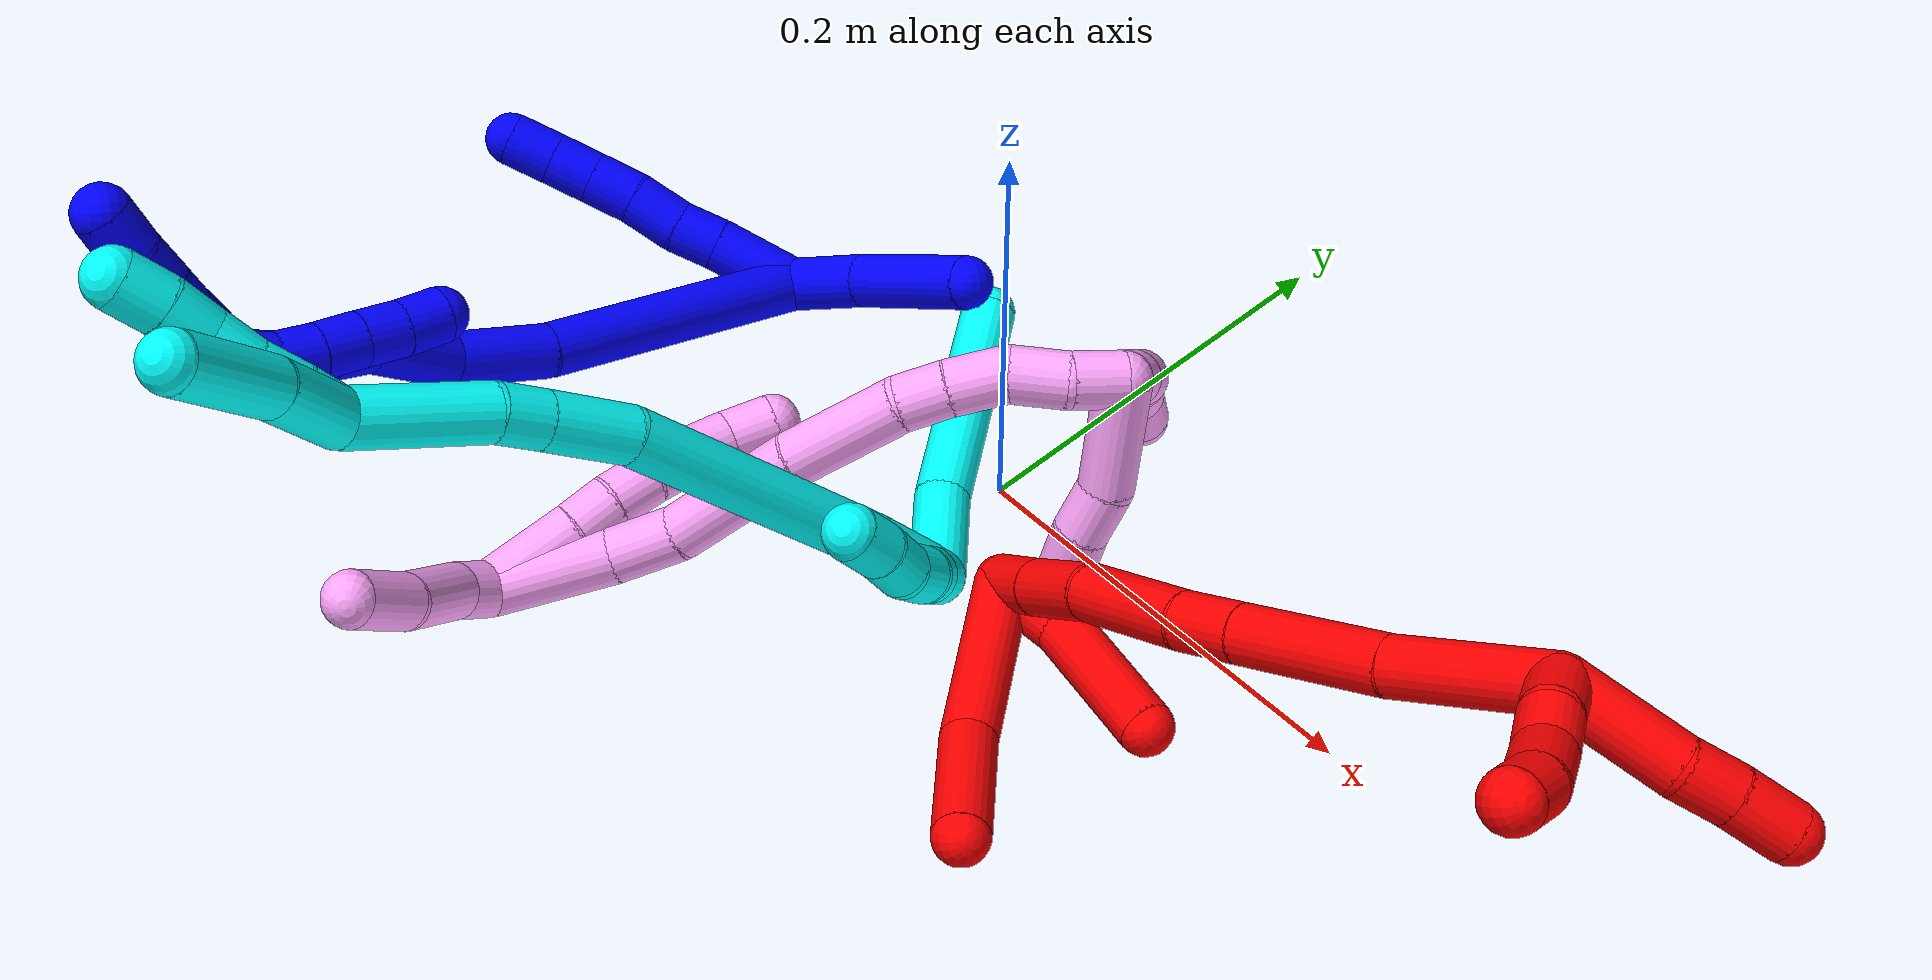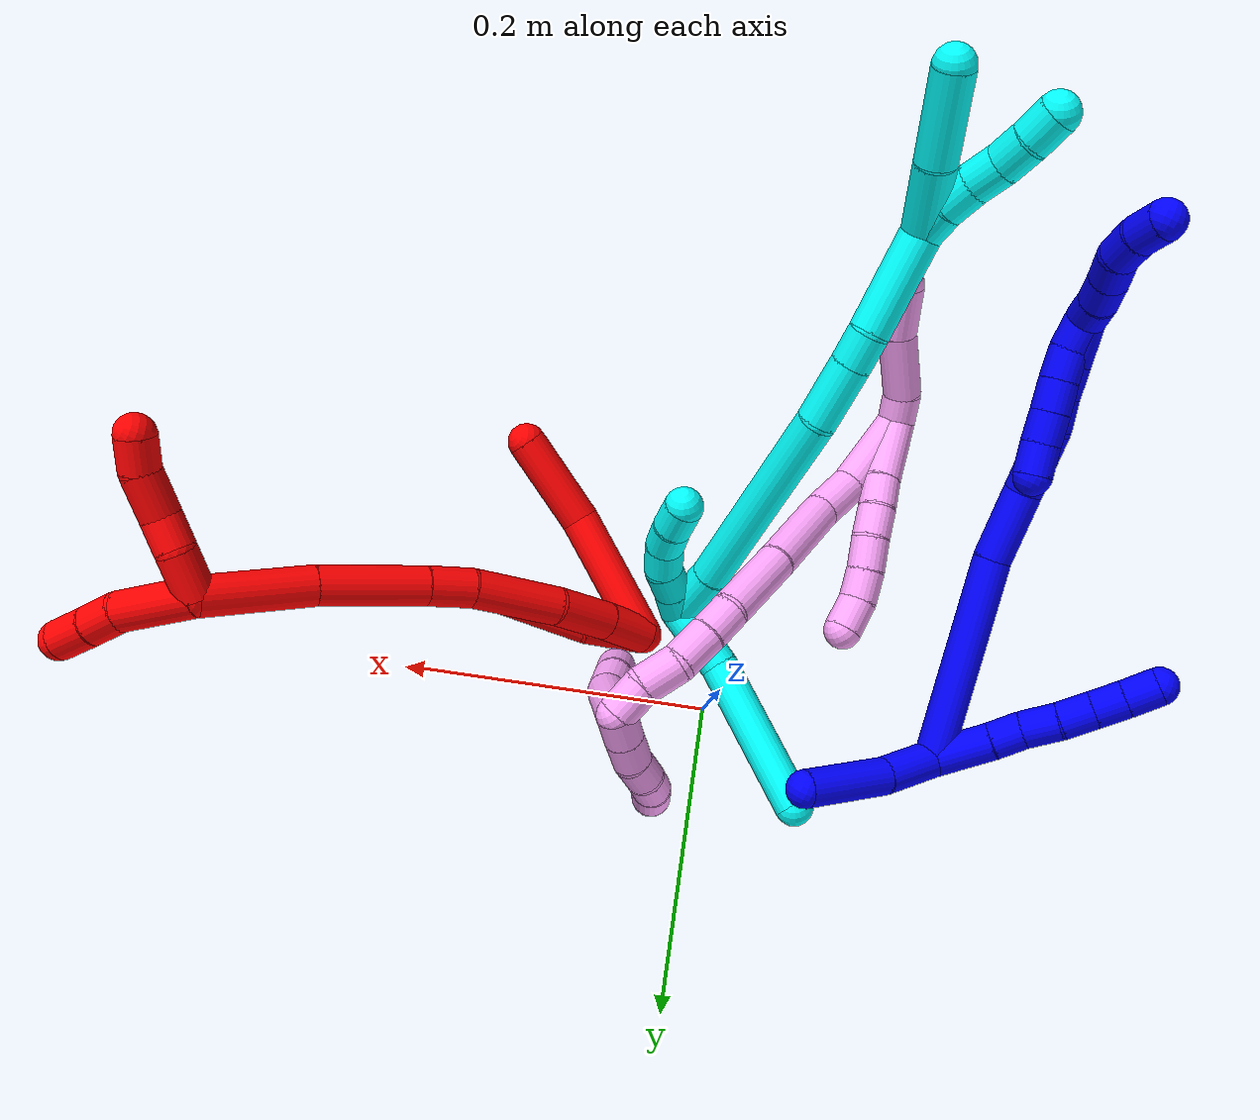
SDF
<sdf version="1.7">
 <world name="default">
  <plugin name="TubeGeneratorPlugin" filename="libtube_generator_plugin.so"/>
  <model name="photoneo_s_sensor">
   <static>1</static>
   <pose>0 0 2 1.57079 1.57079 3.14159</pose>
   <link name="link">
    <inertial><mass>0.1</mass></inertial>
    <sensor name="sensor" type="depth">
     <update_rate>30</update_rate>
     <camera>
      <horizontal_fov>1.22</horizontal_fov>
      <image><width>1920</width><height>1200</height><format>B8G8R8</format></image>
      <clip><near>0.1</near><far>4</far></clip>
      <depth_camera><output>points</output></depth_camera>
     </camera>
     <plugin name="camera_plugin" filename="libgazebo_ros_depth_camera.so">
      <baseline>0.2</baseline>
      <alwaysOn>1</alwaysOn>
      <updateRate>0.0</updateRate>
      <cameraName>camera_ir</cameraName>
      <imageTopicName>/camera/color/image_raw</imageTopicName>
      <cameraInfoTopicName>/camera/color/camera_info</cameraInfoTopicName>
      <depthImageTopicName>/camera/depth/image_raw</depthImageTopicName>
      <depthImageCameraInfoTopicName>/camera/depth/camera_info</depthImageCameraInfoTopicName>
      <pointCloudTopicName>/camera/depth/points</pointCloudTopicName>
      <frameName>fr_optical</frameName>
      <pointCloudCutoff>0.1</pointCloudCutoff>
      <pointCloudCutoffMax>2.0</pointCloudCutoffMax>
      <distortionK1>0</distortionK1>
      <distortionK2>0</distortionK2>
      <distortionK3>0</distortionK3>
      <distortionT1>0</distortionT1>
      <distortionT2>0</distortionT2>
      <CxPrime>0</CxPrime>
      <Cx>0</Cx>
      <Cy>0</Cy>
      <focalLength>0</focalLength>
      <hackBaseline>0</hackBaseline>
     </plugin>
    </sensor>
   </link>
  </model>
  <gravity>0 0 -9.8</gravity>
  <magnetic_field>6e-06 2.3e-05 -4.2e-05</magnetic_field>
  <atmosphere type="adiabatic"/>
  <physics name="default_physics" default="0" type="ode">
   <max_step_size>0.003</max_step_size>
   <real_time_factor>1</real_time_factor>
   <real_time_update_rate>1000</real_time_update_rate>
   <max_contacts>10000</max_contacts>
   <ode>
    <solver>
     <type>quick</type>
     <iters>100</iters>
     <sor>1.3</sor>
     <use_dynamic_moi_rescaling>0</use_dynamic_moi_rescaling>
    </solver>
    <constraints>
     <contact_max_correcting_vel>0</contact_max_correcting_vel>
     <contact_surface_layer>0.001</contact_surface_layer>
     <cfm>0</cfm>
     <erp>0.2</erp>
    </constraints>
   </ode>
  </physics>
  <scene><ambient>0.4 0.4 0.4 1</ambient><background>0.7 0.7 0.7 1</background><shadows>0</shadows></scene>
  <audio><device>default</device></audio>
  <spherical_coordinates>
   <surface_model>EARTH_WGS84</surface_model>
   <latitude_deg>0</latitude_deg>
   <longitude_deg>0</longitude_deg>
   <elevation>0</elevation>
   <heading_deg>0</heading_deg>
  </spherical_coordinates>
  <model name="bin">
   <static>1</static>
   <link name="bottom">
    <collision name="collision-bottom">
     <pose>0 0 -0.01 0 -0 0</pose>
     <geometry><box><size>0.8 0.6 0.02</size></box></geometry>
     <surface>
      <friction><ode><mu>100</mu><mu2>100</mu2></ode></friction>
      <contact><collide_bitmask>65535</collide_bitmask></contact>
     </surface>
    </collision>
   </link>
   <link name="west_wall">
    <collision name="collision-west_wall">
     <pose>-0.41 0 0.1 0 -0 0</pose>
     <geometry><box><size>0.02 0.6 0.2</size></box></geometry>
     <surface>
      <friction><ode><mu>100</mu><mu2>100</mu2></ode></friction>
      <contact><collide_bitmask>65535</collide_bitmask></contact>
     </surface>
    </collision>
   </link>
   <link name="east_wall">
    <collision name="collision-east_wall">
     <pose>0.41 0 0.1 0 -0 0</pose>
     <geometry><box><size>0.02 0.6 0.2</size></box></geometry>
     <surface>
      <friction><ode><mu>100</mu><mu2>100</mu2></ode></friction>
      <contact><collide_bitmask>65535</collide_bitmask></contact>
     </surface>
    </collision>
   </link>
   <link name="south_wall">
    <collision name="collision-south_wall">
     <pose>0 -0.31 0.1 0 -0 0</pose>
     <geometry><box><size>0.8 0.02 0.2</size></box></geometry>
     <surface>
      <friction><ode><mu>100</mu><mu2>100</mu2></ode></friction>
      <contact><collide_bitmask>65535</collide_bitmask></contact>
     </surface>
    </collision>
   </link>
   <link name="north_wall">
    <collision name="collision-north_wall">
     <pose>0 0.31 0.1 0 -0 0</pose>
     <geometry><box><size>0.8 0.02 0.2</size></box></geometry>
     <surface>
      <friction><ode><mu>100</mu><mu2>100</mu2></ode></friction>
      <contact><collide_bitmask>65535</collide_bitmask></contact>
     </surface>
    </collision>
   </link>
  </model>
  <model name="1">
   <static>0</static>
   <link name="1">
    <collision name="collision-cylinder-e_1_2_8">
     <pose>-0.014263 -0.001477 0.013968 0.105359 -0.793061 -0.044148</pose>
     <geometry><cylinder><radius>0.0125</radius><length>0.040037</length></cylinder></geometry>
     <surface>
      <friction><ode><mu>1.16</mu><mu2>1.16</mu2><slip1>0</slip1><slip2>0</slip2></ode></friction>
      <contact><ode><kp>1e+06</kp><kd>1</kd><max_vel>0</max_vel><min_depth>0.001</min_depth></ode></contact>
     </surface>
    </collision>
    <visual name="visual-cylinder-e_1_2_8">
     <pose>-0.014263 -0.001477 0.013968 0.105359 -0.793061 -0.044148</pose>
     <geometry><cylinder><radius>0.0125</radius><length>0.040037</length></cylinder></geometry>
     <material><ambient>0 0 1 1</ambient></material>
    </visual>
    <collision name="collision-cylinder-e_2_8_9">
     <pose>-0.035473 -0.004179 0.035613 0.158178 -0.729283 -0.060486</pose>
     <geometry><cylinder><radius>0.0125</radius><length>0.020851</length></cylinder></geometry>
     <surface>
      <friction><ode><mu>1.16</mu><mu2>1.16</mu2><slip1>0</slip1><slip2>0</slip2></ode></friction>
      <contact><ode><kp>1e+06</kp><kd>1</kd><max_vel>0</max_vel><min_depth>0.001</min_depth></ode></contact>
     </surface>
    </collision>
    <visual name="visual-cylinder-e_2_8_9">
     <pose>-0.035473 -0.004179 0.035613 0.158178 -0.729283 -0.060486</pose>
     <geometry><cylinder><radius>0.0125</radius><length>0.020851</length></cylinder></geometry>
     <material><ambient>0 0 1 1</ambient></material>
    </visual>
    <collision name="collision-cylinder-e_3_9_10">
     <pose>-0.051505 -0.005282 0.051379 -0.01495 -0.84327 0.006706</pose>
     <geometry><cylinder><radius>0.0125</radius><length>0.024331</length></cylinder></geometry>
     <surface>
      <friction><ode><mu>1.16</mu><mu2>1.16</mu2><slip1>0</slip1><slip2>0</slip2></ode></friction>
      <contact><ode><kp>1e+06</kp><kd>1</kd><max_vel>0</max_vel><min_depth>0.001</min_depth></ode></contact>
     </surface>
    </collision>
    <visual name="visual-cylinder-e_3_9_10">
     <pose>-0.051505 -0.005282 0.051379 -0.01495 -0.84327 0.006706</pose>
     <geometry><cylinder><radius>0.0125</radius><length>0.024331</length></cylinder></geometry>
     <material><ambient>0 0 1 1</ambient></material>
    </visual>
    <collision name="collision-cylinder-e_4_10_11">
     <pose>-0.068132 -0.006142 0.067429 0.122533 -0.754654 -0.048613</pose>
     <geometry><cylinder><radius>0.0125</radius><length>0.022017</length></cylinder></geometry>
     <surface>
      <friction><ode><mu>1.16</mu><mu2>1.16</mu2><slip1>0</slip1><slip2>0</slip2></ode></friction>
      <contact><ode><kp>1e+06</kp><kd>1</kd><max_vel>0</max_vel><min_depth>0.001</min_depth></ode></contact>
     </surface>
    </collision>
    <visual name="visual-cylinder-e_4_10_11">
     <pose>-0.068132 -0.006142 0.067429 0.122533 -0.754654 -0.048613</pose>
     <geometry><cylinder><radius>0.0125</radius><length>0.022017</length></cylinder></geometry>
     <material><ambient>0 0 1 1</ambient></material>
    </visual>
    <collision name="collision-cylinder-e_5_11_12">
     <pose>-0.082734 -0.00802 0.08293 0.118575 -0.748896 -0.046645</pose>
     <geometry><cylinder><radius>0.0125</radius><length>0.02074</length></cylinder></geometry>
     <surface>
      <friction><ode><mu>1.16</mu><mu2>1.16</mu2><slip1>0</slip1><slip2>0</slip2></ode></friction>
      <contact><ode><kp>1e+06</kp><kd>1</kd><max_vel>0</max_vel><min_depth>0.001</min_depth></ode></contact>
     </surface>
    </collision>
    <visual name="visual-cylinder-e_5_11_12">
     <pose>-0.082734 -0.00802 0.08293 0.118575 -0.748896 -0.046645</pose>
     <geometry><cylinder><radius>0.0125</radius><length>0.02074</length></cylinder></geometry>
     <material><ambient>0 0 1 1</ambient></material>
    </visual>
    <collision name="collision-cylinder-e_6_12_6">
     <pose>-0.096985 -0.009576 0.098787 0.078838 -0.71153 -0.029307</pose>
     <geometry><cylinder><radius>0.0125</radius><length>0.022024</length></cylinder></geometry>
     <surface>
      <friction><ode><mu>1.16</mu><mu2>1.16</mu2><slip1>0</slip1><slip2>0</slip2></ode></friction>
      <contact><ode><kp>1e+06</kp><kd>1</kd><max_vel>0</max_vel><min_depth>0.001</min_depth></ode></contact>
     </surface>
    </collision>
    <visual name="visual-cylinder-e_6_12_6">
     <pose>-0.096985 -0.009576 0.098787 0.078838 -0.71153 -0.029307</pose>
     <geometry><cylinder><radius>0.0125</radius><length>0.022024</length></cylinder></geometry>
     <material><ambient>0 0 1 1</ambient></material>
    </visual>
    <collision name="collision-cylinder-e_1_2_13">
     <pose>0.010304 0.013974 -0.009724 -2.17875 0.544269 -0.981209</pose>
     <geometry><cylinder><radius>0.0125</radius><length>0.0398</length></cylinder></geometry>
     <surface>
      <friction><ode><mu>1.16</mu><mu2>1.16</mu2><slip1>0</slip1><slip2>0</slip2></ode></friction>
      <contact><ode><kp>1e+06</kp><kd>1</kd><max_vel>0</max_vel><min_depth>0.001</min_depth></ode></contact>
     </surface>
    </collision>
    <visual name="visual-cylinder-e_1_2_13">
     <pose>0.010304 0.013974 -0.009724 -2.17875 0.544269 -0.981209</pose>
     <geometry><cylinder><radius>0.0125</radius><length>0.0398</length></cylinder></geometry>
     <material><ambient>0 0 1 1</ambient></material>
    </visual>
    <collision name="collision-cylinder-e_2_13_5">
     <pose>0.038537 0.049664 -0.030078 -2.026 0.638073 -0.973868</pose>
     <geometry><cylinder><radius>0.0125</radius><length>0.0602</length></cylinder></geometry>
     <surface>
      <friction><ode><mu>1.16</mu><mu2>1.16</mu2><slip1>0</slip1><slip2>0</slip2></ode></friction>
      <contact><ode><kp>1e+06</kp><kd>1</kd><max_vel>0</max_vel><min_depth>0.001</min_depth></ode></contact>
     </surface>
    </collision>
    <visual name="visual-cylinder-e_2_13_5">
     <pose>0.038537 0.049664 -0.030078 -2.026 0.638073 -0.973868</pose>
     <geometry><cylinder><radius>0.0125</radius><length>0.0602</length></cylinder></geometry>
     <material><ambient>0 0 1 1</ambient></material>
    </visual>
    <collision name="collision-cylinder-e_1_2_14">
     <pose>0.011896 -0.000566 0.06716 0.008432 0.175311 0.000741</pose>
     <geometry><cylinder><radius>0.0125</radius><length>0.136416</length></cylinder></geometry>
     <surface>
      <friction><ode><mu>1.16</mu><mu2>1.16</mu2><slip1>0</slip1><slip2>0</slip2></ode></friction>
      <contact><ode><kp>1e+06</kp><kd>1</kd><max_vel>0</max_vel><min_depth>0.001</min_depth></ode></contact>
     </surface>
    </collision>
    <visual name="visual-cylinder-e_1_2_14">
     <pose>0.011896 -0.000566 0.06716 0.008432 0.175311 0.000741</pose>
     <geometry><cylinder><radius>0.0125</radius><length>0.136416</length></cylinder></geometry>
     <material><ambient>0 0 1 1</ambient></material>
    </visual>
    <collision name="collision-cylinder-e_2_14_15">
     <pose>0.024558 0.00012 0.158413 -0.051962 0.03169 -0.000824</pose>
     <geometry><cylinder><radius>0.0125</radius><length>0.048275</length></cylinder></geometry>
     <surface>
      <friction><ode><mu>1.16</mu><mu2>1.16</mu2><slip1>0</slip1><slip2>0</slip2></ode></friction>
      <contact><ode><kp>1e+06</kp><kd>1</kd><max_vel>0</max_vel><min_depth>0.001</min_depth></ode></contact>
     </surface>
    </collision>
    <visual name="visual-cylinder-e_2_14_15">
     <pose>0.024558 0.00012 0.158413 -0.051962 0.03169 -0.000824</pose>
     <geometry><cylinder><radius>0.0125</radius><length>0.048275</length></cylinder></geometry>
     <material><ambient>0 0 1 1</ambient></material>
    </visual>
    <collision name="collision-cylinder-e_3_15_16">
     <pose>0.025273 0.010077 0.203443 -0.393975 -0.002183 0.000436</pose>
     <geometry><cylinder><radius>0.0125</radius><length>0.045349</length></cylinder></geometry>
     <surface>
      <friction><ode><mu>1.16</mu><mu2>1.16</mu2><slip1>0</slip1><slip2>0</slip2></ode></friction>
      <contact><ode><kp>1e+06</kp><kd>1</kd><max_vel>0</max_vel><min_depth>0.001</min_depth></ode></contact>
     </surface>
    </collision>
    <visual name="visual-cylinder-e_3_15_16">
     <pose>0.025273 0.010077 0.203443 -0.393975 -0.002183 0.000436</pose>
     <geometry><cylinder><radius>0.0125</radius><length>0.045349</length></cylinder></geometry>
     <material><ambient>0 0 1 1</ambient></material>
    </visual>
    <collision name="collision-cylinder-e_4_16_17">
     <pose>0.027312 0.020319 0.234346 -0.153102 0.20421 -0.015717</pose>
     <geometry><cylinder><radius>0.0125</radius><length>0.020595</length></cylinder></geometry>
     <surface>
      <friction><ode><mu>1.16</mu><mu2>1.16</mu2><slip1>0</slip1><slip2>0</slip2></ode></friction>
      <contact><ode><kp>1e+06</kp><kd>1</kd><max_vel>0</max_vel><min_depth>0.001</min_depth></ode></contact>
     </surface>
    </collision>
    <visual name="visual-cylinder-e_4_16_17">
     <pose>0.027312 0.020319 0.234346 -0.153102 0.20421 -0.015717</pose>
     <geometry><cylinder><radius>0.0125</radius><length>0.020595</length></cylinder></geometry>
     <material><ambient>0 0 1 1</ambient></material>
    </visual>
    <collision name="collision-cylinder-e_5_17_18">
     <pose>0.030735 0.022565 0.254737 -0.067795 0.127011 -0.004313</pose>
     <geometry><cylinder><radius>0.0125</radius><length>0.021069</length></cylinder></geometry>
     <surface>
      <friction><ode><mu>1.16</mu><mu2>1.16</mu2><slip1>0</slip1><slip2>0</slip2></ode></friction>
      <contact><ode><kp>1e+06</kp><kd>1</kd><max_vel>0</max_vel><min_depth>0.001</min_depth></ode></contact>
     </surface>
    </collision>
    <visual name="visual-cylinder-e_5_17_18">
     <pose>0.030735 0.022565 0.254737 -0.067795 0.127011 -0.004313</pose>
     <geometry><cylinder><radius>0.0125</radius><length>0.021069</length></cylinder></geometry>
     <material><ambient>0 0 1 1</ambient></material>
    </visual>
    <collision name="collision-cylinder-e_6_18_1">
     <pose>0.033605 0.027721 0.278505 -0.321838 0.108799 -0.017678</pose>
     <geometry><cylinder><radius>0.0125</radius><length>0.028296</length></cylinder></geometry>
     <surface>
      <friction><ode><mu>1.16</mu><mu2>1.16</mu2><slip1>0</slip1><slip2>0</slip2></ode></friction>
      <contact><ode><kp>1e+06</kp><kd>1</kd><max_vel>0</max_vel><min_depth>0.001</min_depth></ode></contact>
     </surface>
    </collision>
    <visual name="visual-cylinder-e_6_18_1">
     <pose>0.033605 0.027721 0.278505 -0.321838 0.108799 -0.017678</pose>
     <geometry><cylinder><radius>0.0125</radius><length>0.028296</length></cylinder></geometry>
     <material><ambient>0 0 1 1</ambient></material>
    </visual>
    <collision name="collision-cylinder-e_1_1_19">
     <pose>0.033252 0.040089 0.297654 -0.938126 -0.190039 0.096525</pose>
     <geometry><cylinder><radius>0.0125</radius><length>0.02</length></cylinder></geometry>
     <surface>
      <friction><ode><mu>1.16</mu><mu2>1.16</mu2><slip1>0</slip1><slip2>0</slip2></ode></friction>
      <contact><ode><kp>1e+06</kp><kd>1</kd><max_vel>0</max_vel><min_depth>0.001</min_depth></ode></contact>
     </surface>
    </collision>
    <visual name="visual-cylinder-e_1_1_19">
     <pose>0.033252 0.040089 0.297654 -0.938126 -0.190039 0.096525</pose>
     <geometry><cylinder><radius>0.0125</radius><length>0.02</length></cylinder></geometry>
     <material><ambient>0 0 1 1</ambient></material>
    </visual>
    <collision name="collision-cylinder-e_2_19_20">
     <pose>0.03061 0.055726 0.309775 -0.885115 -0.075442 0.035766</pose>
     <geometry><cylinder><radius>0.0125</radius><length>0.02</length></cylinder></geometry>
     <surface>
      <friction><ode><mu>1.16</mu><mu2>1.16</mu2><slip1>0</slip1><slip2>0</slip2></ode></friction>
      <contact><ode><kp>1e+06</kp><kd>1</kd><max_vel>0</max_vel><min_depth>0.001</min_depth></ode></contact>
     </surface>
    </collision>
    <visual name="visual-cylinder-e_2_19_20">
     <pose>0.03061 0.055726 0.309775 -0.885115 -0.075442 0.035766</pose>
     <geometry><cylinder><radius>0.0125</radius><length>0.02</length></cylinder></geometry>
     <material><ambient>0 0 1 1</ambient></material>
    </visual>
    <collision name="collision-cylinder-e_3_20_21">
     <pose>0.029516 0.07159 0.321879 -0.952816 -0.03397 0.017532</pose>
     <geometry><cylinder><radius>0.0125</radius><length>0.02</length></cylinder></geometry>
     <surface>
      <friction><ode><mu>1.16</mu><mu2>1.16</mu2><slip1>0</slip1><slip2>0</slip2></ode></friction>
      <contact><ode><kp>1e+06</kp><kd>1</kd><max_vel>0</max_vel><min_depth>0.001</min_depth></ode></contact>
     </surface>
    </collision>
    <visual name="visual-cylinder-e_3_20_21">
     <pose>0.029516 0.07159 0.321879 -0.952816 -0.03397 0.017532</pose>
     <geometry><cylinder><radius>0.0125</radius><length>0.02</length></cylinder></geometry>
     <material><ambient>0 0 1 1</ambient></material>
    </visual>
    <collision name="collision-cylinder-e_4_21_22">
     <pose>0.025882 0.086727 0.334015 -0.833818 -0.335724 0.149814</pose>
     <geometry><cylinder><radius>0.0125</radius><length>0.02</length></cylinder></geometry>
     <surface>
      <friction><ode><mu>1.16</mu><mu2>1.16</mu2><slip1>0</slip1><slip2>0</slip2></ode></friction>
      <contact><ode><kp>1e+06</kp><kd>1</kd><max_vel>0</max_vel><min_depth>0.001</min_depth></ode></contact>
     </surface>
    </collision>
    <visual name="visual-cylinder-e_4_21_22">
     <pose>0.025882 0.086727 0.334015 -0.833818 -0.335724 0.149814</pose>
     <geometry><cylinder><radius>0.0125</radius><length>0.02</length></cylinder></geometry>
     <material><ambient>0 0 1 1</ambient></material>
    </visual>
    <collision name="collision-cylinder-e_5_22_4">
     <pose>0.01727 0.099962 0.346082 -0.828926 -0.560738 0.252026</pose>
     <geometry><cylinder><radius>0.0125</radius><length>0.02</length></cylinder></geometry>
     <surface>
      <friction><ode><mu>1.16</mu><mu2>1.16</mu2><slip1>0</slip1><slip2>0</slip2></ode></friction>
      <contact><ode><kp>1e+06</kp><kd>1</kd><max_vel>0</max_vel><min_depth>0.001</min_depth></ode></contact>
     </surface>
    </collision>
    <visual name="visual-cylinder-e_5_22_4">
     <pose>0.01727 0.099962 0.346082 -0.828926 -0.560738 0.252026</pose>
     <geometry><cylinder><radius>0.0125</radius><length>0.02</length></cylinder></geometry>
     <material><ambient>0 0 1 1</ambient></material>
    </visual>
    <collision name="collision-cylinder-e_1_1_23">
     <pose>0.035616 0.03048 0.282003 2.97165 0.04747 0.543616</pose>
     <geometry><cylinder><radius>0.0125</radius><length>0.02</length></cylinder></geometry>
     <surface>
      <friction><ode><mu>1.16</mu><mu2>1.16</mu2><slip1>0</slip1><slip2>0</slip2></ode></friction>
      <contact><ode><kp>1e+06</kp><kd>1</kd><max_vel>0</max_vel><min_depth>0.001</min_depth></ode></contact>
     </surface>
    </collision>
    <visual name="visual-cylinder-e_1_1_23">
     <pose>0.035616 0.03048 0.282003 2.97165 0.04747 0.543616</pose>
     <geometry><cylinder><radius>0.0125</radius><length>0.02</length></cylinder></geometry>
     <material><ambient>0 0 1 1</ambient></material>
    </visual>
    <collision name="collision-cylinder-e_2_23_24">
     <pose>0.034683 0.028879 0.262258 -3.13268 -0.141193 3.01573</pose>
     <geometry><cylinder><radius>0.0125</radius><length>0.02</length></cylinder></geometry>
     <surface>
      <friction><ode><mu>1.16</mu><mu2>1.16</mu2><slip1>0</slip1><slip2>0</slip2></ode></friction>
      <contact><ode><kp>1e+06</kp><kd>1</kd><max_vel>0</max_vel><min_depth>0.001</min_depth></ode></contact>
     </surface>
    </collision>
    <visual name="visual-cylinder-e_2_23_24">
     <pose>0.034683 0.028879 0.262258 -3.13268 -0.141193 3.01573</pose>
     <geometry><cylinder><radius>0.0125</radius><length>0.02</length></cylinder></geometry>
     <material><ambient>0 0 1 1</ambient></material>
    </visual>
    <collision name="collision-cylinder-e_3_24_25">
     <pose>0.03132 0.029214 0.242554 -3.11643 -0.196826 2.88809</pose>
     <geometry><cylinder><radius>0.0125</radius><length>0.02</length></cylinder></geometry>
     <surface>
      <friction><ode><mu>1.16</mu><mu2>1.16</mu2><slip1>0</slip1><slip2>0</slip2></ode></friction>
      <contact><ode><kp>1e+06</kp><kd>1</kd><max_vel>0</max_vel><min_depth>0.001</min_depth></ode></contact>
     </surface>
    </collision>
    <visual name="visual-cylinder-e_3_24_25">
     <pose>0.03132 0.029214 0.242554 -3.11643 -0.196826 2.88809</pose>
     <geometry><cylinder><radius>0.0125</radius><length>0.02</length></cylinder></geometry>
     <material><ambient>0 0 1 1</ambient></material>
    </visual>
    <collision name="collision-cylinder-e_4_25_26">
     <pose>0.027661 0.029646 0.222898 -3.12285 -0.17117 2.924</pose>
     <geometry><cylinder><radius>0.0125</radius><length>0.02</length></cylinder></geometry>
     <surface>
      <friction><ode><mu>1.16</mu><mu2>1.16</mu2><slip1>0</slip1><slip2>0</slip2></ode></friction>
      <contact><ode><kp>1e+06</kp><kd>1</kd><max_vel>0</max_vel><min_depth>0.001</min_depth></ode></contact>
     </surface>
    </collision>
    <visual name="visual-cylinder-e_4_25_26">
     <pose>0.027661 0.029646 0.222898 -3.12285 -0.17117 2.924</pose>
     <geometry><cylinder><radius>0.0125</radius><length>0.02</length></cylinder></geometry>
     <material><ambient>0 0 1 1</ambient></material>
    </visual>
    <collision name="collision-cylinder-e_5_26_3">
     <pose>0.023692 0.030442 0.203325 -3.07877 -0.228583 2.60719</pose>
     <geometry><cylinder><radius>0.0125</radius><length>0.02</length></cylinder></geometry>
     <surface>
      <friction><ode><mu>1.16</mu><mu2>1.16</mu2><slip1>0</slip1><slip2>0</slip2></ode></friction>
      <contact><ode><kp>1e+06</kp><kd>1</kd><max_vel>0</max_vel><min_depth>0.001</min_depth></ode></contact>
     </surface>
    </collision>
    <visual name="visual-cylinder-e_5_26_3">
     <pose>0.023692 0.030442 0.203325 -3.07877 -0.228583 2.60719</pose>
     <geometry><cylinder><radius>0.0125</radius><length>0.02</length></cylinder></geometry>
     <material><ambient>0 0 1 1</ambient></material>
    </visual>
    <collision name="collision-sphere-3">
     <pose>0.021426 0.031053 0.193604 0 -0 0</pose>
     <geometry><sphere><radius>0.0125</radius></sphere></geometry>
     <surface>
      <friction><ode><mu>1.16</mu><mu2>1.16</mu2><slip1>0</slip1><slip2>0</slip2></ode></friction>
      <contact><ode><kp>1e+06</kp><kd>1</kd><max_vel>0</max_vel><min_depth>0.001</min_depth></ode></contact>
     </surface>
    </collision>
    <visual name="visual-sphere-3">
     <pose>0.021426 0.031053 0.193604 0 -0 0</pose>
     <geometry><sphere><radius>0.0125</radius></sphere></geometry>
     <material><ambient>0 0 1 1</ambient></material>
    </visual>
    <collision name="collision-sphere-26">
     <pose>0.025958 0.02983 0.213046 0 -0 0</pose>
     <geometry><sphere><radius>0.0125</radius></sphere></geometry>
     <surface>
      <friction><ode><mu>1.16</mu><mu2>1.16</mu2><slip1>0</slip1><slip2>0</slip2></ode></friction>
      <contact><ode><kp>1e+06</kp><kd>1</kd><max_vel>0</max_vel><min_depth>0.001</min_depth></ode></contact>
     </surface>
    </collision>
    <visual name="visual-sphere-26">
     <pose>0.025958 0.02983 0.213046 0 -0 0</pose>
     <geometry><sphere><radius>0.0125</radius></sphere></geometry>
     <material><ambient>0 0 1 1</ambient></material>
    </visual>
    <collision name="collision-sphere-25">
     <pose>0.029365 0.029461 0.23275 0 -0 0</pose>
     <geometry><sphere><radius>0.0125</radius></sphere></geometry>
     <surface>
      <friction><ode><mu>1.16</mu><mu2>1.16</mu2><slip1>0</slip1><slip2>0</slip2></ode></friction>
      <contact><ode><kp>1e+06</kp><kd>1</kd><max_vel>0</max_vel><min_depth>0.001</min_depth></ode></contact>
     </surface>
    </collision>
    <visual name="visual-sphere-25">
     <pose>0.029365 0.029461 0.23275 0 -0 0</pose>
     <geometry><sphere><radius>0.0125</radius></sphere></geometry>
     <material><ambient>0 0 1 1</ambient></material>
    </visual>
    <collision name="collision-sphere-24">
     <pose>0.033276 0.028968 0.252358 0 -0 0</pose>
     <geometry><sphere><radius>0.0125</radius></sphere></geometry>
     <surface>
      <friction><ode><mu>1.16</mu><mu2>1.16</mu2><slip1>0</slip1><slip2>0</slip2></ode></friction>
      <contact><ode><kp>1e+06</kp><kd>1</kd><max_vel>0</max_vel><min_depth>0.001</min_depth></ode></contact>
     </surface>
    </collision>
    <visual name="visual-sphere-24">
     <pose>0.033276 0.028968 0.252358 0 -0 0</pose>
     <geometry><sphere><radius>0.0125</radius></sphere></geometry>
     <material><ambient>0 0 1 1</ambient></material>
    </visual>
    <collision name="collision-sphere-23">
     <pose>0.03609 0.028791 0.272158 0 -0 0</pose>
     <geometry><sphere><radius>0.0125</radius></sphere></geometry>
     <surface>
      <friction><ode><mu>1.16</mu><mu2>1.16</mu2><slip1>0</slip1><slip2>0</slip2></ode></friction>
      <contact><ode><kp>1e+06</kp><kd>1</kd><max_vel>0</max_vel><min_depth>0.001</min_depth></ode></contact>
     </surface>
    </collision>
    <visual name="visual-sphere-23">
     <pose>0.03609 0.028791 0.272158 0 -0 0</pose>
     <geometry><sphere><radius>0.0125</radius></sphere></geometry>
     <material><ambient>0 0 1 1</ambient></material>
    </visual>
    <collision name="collision-sphere-4">
     <pose>0.011952 0.106205 0.351804 0 -0 0</pose>
     <geometry><sphere><radius>0.0125</radius></sphere></geometry>
     <surface>
      <friction><ode><mu>1.16</mu><mu2>1.16</mu2><slip1>0</slip1><slip2>0</slip2></ode></friction>
      <contact><ode><kp>1e+06</kp><kd>1</kd><max_vel>0</max_vel><min_depth>0.001</min_depth></ode></contact>
     </surface>
    </collision>
    <visual name="visual-sphere-4">
     <pose>0.011952 0.106205 0.351804 0 -0 0</pose>
     <geometry><sphere><radius>0.0125</radius></sphere></geometry>
     <material><ambient>0 0 1 1</ambient></material>
    </visual>
    <collision name="collision-sphere-22">
     <pose>0.022588 0.093719 0.34036 0 -0 0</pose>
     <geometry><sphere><radius>0.0125</radius></sphere></geometry>
     <surface>
      <friction><ode><mu>1.16</mu><mu2>1.16</mu2><slip1>0</slip1><slip2>0</slip2></ode></friction>
      <contact><ode><kp>1e+06</kp><kd>1</kd><max_vel>0</max_vel><min_depth>0.001</min_depth></ode></contact>
     </surface>
    </collision>
    <visual name="visual-sphere-22">
     <pose>0.022588 0.093719 0.34036 0 -0 0</pose>
     <geometry><sphere><radius>0.0125</radius></sphere></geometry>
     <material><ambient>0 0 1 1</ambient></material>
    </visual>
    <collision name="collision-sphere-21">
     <pose>0.029177 0.079736 0.32767 0 -0 0</pose>
     <geometry><sphere><radius>0.0125</radius></sphere></geometry>
     <surface>
      <friction><ode><mu>1.16</mu><mu2>1.16</mu2><slip1>0</slip1><slip2>0</slip2></ode></friction>
      <contact><ode><kp>1e+06</kp><kd>1</kd><max_vel>0</max_vel><min_depth>0.001</min_depth></ode></contact>
     </surface>
    </collision>
    <visual name="visual-sphere-21">
     <pose>0.029177 0.079736 0.32767 0 -0 0</pose>
     <geometry><sphere><radius>0.0125</radius></sphere></geometry>
     <material><ambient>0 0 1 1</ambient></material>
    </visual>
    <collision name="collision-sphere-20">
     <pose>0.029856 0.063444 0.316089 0 -0 0</pose>
     <geometry><sphere><radius>0.0125</radius></sphere></geometry>
     <surface>
      <friction><ode><mu>1.16</mu><mu2>1.16</mu2><slip1>0</slip1><slip2>0</slip2></ode></friction>
      <contact><ode><kp>1e+06</kp><kd>1</kd><max_vel>0</max_vel><min_depth>0.001</min_depth></ode></contact>
     </surface>
    </collision>
    <visual name="visual-sphere-20">
     <pose>0.029856 0.063444 0.316089 0 -0 0</pose>
     <geometry><sphere><radius>0.0125</radius></sphere></geometry>
     <material><ambient>0 0 1 1</ambient></material>
    </visual>
    <collision name="collision-sphere-12">
     <pose>-0.089794 -0.008919 0.090473 0 -0 0</pose>
     <geometry><sphere><radius>0.0125</radius></sphere></geometry>
     <surface>
      <friction><ode><mu>1.16</mu><mu2>1.16</mu2><slip1>0</slip1><slip2>0</slip2></ode></friction>
      <contact><ode><kp>1e+06</kp><kd>1</kd><max_vel>0</max_vel><min_depth>0.001</min_depth></ode></contact>
     </surface>
    </collision>
    <visual name="visual-sphere-12">
     <pose>-0.089794 -0.008919 0.090473 0 -0 0</pose>
     <geometry><sphere><radius>0.0125</radius></sphere></geometry>
     <material><ambient>0 0 1 1</ambient></material>
    </visual>
    <collision name="collision-sphere-11">
     <pose>-0.075673 -0.007122 0.075388 0 -0 0</pose>
     <geometry><sphere><radius>0.0125</radius></sphere></geometry>
     <surface>
      <friction><ode><mu>1.16</mu><mu2>1.16</mu2><slip1>0</slip1><slip2>0</slip2></ode></friction>
      <contact><ode><kp>1e+06</kp><kd>1</kd><max_vel>0</max_vel><min_depth>0.001</min_depth></ode></contact>
     </surface>
    </collision>
    <visual name="visual-sphere-11">
     <pose>-0.075673 -0.007122 0.075388 0 -0 0</pose>
     <geometry><sphere><radius>0.0125</radius></sphere></geometry>
     <material><ambient>0 0 1 1</ambient></material>
    </visual>
    <collision name="collision-sphere-10">
     <pose>-0.060591 -0.005161 0.059469 0 -0 0</pose>
     <geometry><sphere><radius>0.0125</radius></sphere></geometry>
     <surface>
      <friction><ode><mu>1.16</mu><mu2>1.16</mu2><slip1>0</slip1><slip2>0</slip2></ode></friction>
      <contact><ode><kp>1e+06</kp><kd>1</kd><max_vel>0</max_vel><min_depth>0.001</min_depth></ode></contact>
     </surface>
    </collision>
    <visual name="visual-sphere-10">
     <pose>-0.060591 -0.005161 0.059469 0 -0 0</pose>
     <geometry><sphere><radius>0.0125</radius></sphere></geometry>
     <material><ambient>0 0 1 1</ambient></material>
    </visual>
    <collision name="collision-sphere-9">
     <pose>-0.04242 -0.005403 0.04329 0 -0 0</pose>
     <geometry><sphere><radius>0.0125</radius></sphere></geometry>
     <surface>
      <friction><ode><mu>1.16</mu><mu2>1.16</mu2><slip1>0</slip1><slip2>0</slip2></ode></friction>
      <contact><ode><kp>1e+06</kp><kd>1</kd><max_vel>0</max_vel><min_depth>0.001</min_depth></ode></contact>
     </surface>
    </collision>
    <visual name="visual-sphere-9">
     <pose>-0.04242 -0.005403 0.04329 0 -0 0</pose>
     <geometry><sphere><radius>0.0125</radius></sphere></geometry>
     <material><ambient>0 0 1 1</ambient></material>
    </visual>
    <collision name="collision-sphere-2">
     <geometry><sphere><radius>0.0125</radius></sphere></geometry>
     <surface>
      <friction><ode><mu>1.16</mu><mu2>1.16</mu2><slip1>0</slip1><slip2>0</slip2></ode></friction>
      <contact><ode><kp>1e+06</kp><kd>1</kd><max_vel>0</max_vel><min_depth>0.001</min_depth></ode></contact>
     </surface>
    </collision>
    <visual name="visual-sphere-2">
     <geometry><sphere><radius>0.0125</radius></sphere></geometry>
     <material><ambient>0 0 1 1</ambient></material>
    </visual>
    <collision name="collision-sphere-19">
     <pose>0.031363 0.048008 0.303461 0 -0 0</pose>
     <geometry><sphere><radius>0.0125</radius></sphere></geometry>
     <surface>
      <friction><ode><mu>1.16</mu><mu2>1.16</mu2><slip1>0</slip1><slip2>0</slip2></ode></friction>
      <contact><ode><kp>1e+06</kp><kd>1</kd><max_vel>0</max_vel><min_depth>0.001</min_depth></ode></contact>
     </surface>
    </collision>
    <visual name="visual-sphere-19">
     <pose>0.031363 0.048008 0.303461 0 -0 0</pose>
     <geometry><sphere><radius>0.0125</radius></sphere></geometry>
     <material><ambient>0 0 1 1</ambient></material>
    </visual>
    <collision name="collision-sphere-8">
     <pose>-0.028526 -0.002954 0.027937 0 -0 0</pose>
     <geometry><sphere><radius>0.0125</radius></sphere></geometry>
     <surface>
      <friction><ode><mu>1.16</mu><mu2>1.16</mu2><slip1>0</slip1><slip2>0</slip2></ode></friction>
      <contact><ode><kp>1e+06</kp><kd>1</kd><max_vel>0</max_vel><min_depth>0.001</min_depth></ode></contact>
     </surface>
    </collision>
    <visual name="visual-sphere-8">
     <pose>-0.028526 -0.002954 0.027937 0 -0 0</pose>
     <geometry><sphere><radius>0.0125</radius></sphere></geometry>
     <material><ambient>0 0 1 1</ambient></material>
    </visual>
    <collision name="collision-sphere-6">
     <pose>-0.104176 -0.010233 0.107101 0 -0 0</pose>
     <geometry><sphere><radius>0.0125</radius></sphere></geometry>
     <surface>
      <friction><ode><mu>1.16</mu><mu2>1.16</mu2><slip1>0</slip1><slip2>0</slip2></ode></friction>
      <contact><ode><kp>1e+06</kp><kd>1</kd><max_vel>0</max_vel><min_depth>0.001</min_depth></ode></contact>
     </surface>
    </collision>
    <visual name="visual-sphere-6">
     <pose>-0.104176 -0.010233 0.107101 0 -0 0</pose>
     <geometry><sphere><radius>0.0125</radius></sphere></geometry>
     <material><ambient>0 0 1 1</ambient></material>
    </visual>
    <collision name="collision-sphere-13">
     <pose>0.020608 0.027948 -0.019449 0 -0 0</pose>
     <geometry><sphere><radius>0.0125</radius></sphere></geometry>
     <surface>
      <friction><ode><mu>1.16</mu><mu2>1.16</mu2><slip1>0</slip1><slip2>0</slip2></ode></friction>
      <contact><ode><kp>1e+06</kp><kd>1</kd><max_vel>0</max_vel><min_depth>0.001</min_depth></ode></contact>
     </surface>
    </collision>
    <visual name="visual-sphere-13">
     <pose>0.020608 0.027948 -0.019449 0 -0 0</pose>
     <geometry><sphere><radius>0.0125</radius></sphere></geometry>
     <material><ambient>0 0 1 1</ambient></material>
    </visual>
    <collision name="collision-sphere-5">
     <pose>0.056466 0.07138 -0.040708 0 -0 0</pose>
     <geometry><sphere><radius>0.0125</radius></sphere></geometry>
     <surface>
      <friction><ode><mu>1.16</mu><mu2>1.16</mu2><slip1>0</slip1><slip2>0</slip2></ode></friction>
      <contact><ode><kp>1e+06</kp><kd>1</kd><max_vel>0</max_vel><min_depth>0.001</min_depth></ode></contact>
     </surface>
    </collision>
    <visual name="visual-sphere-5">
     <pose>0.056466 0.07138 -0.040708 0 -0 0</pose>
     <geometry><sphere><radius>0.0125</radius></sphere></geometry>
     <material><ambient>0 0 1 1</ambient></material>
    </visual>
    <collision name="collision-sphere-14">
     <pose>0.023793 -0.001133 0.13432 0 -0 0</pose>
     <geometry><sphere><radius>0.0125</radius></sphere></geometry>
     <surface>
      <friction><ode><mu>1.16</mu><mu2>1.16</mu2><slip1>0</slip1><slip2>0</slip2></ode></friction>
      <contact><ode><kp>1e+06</kp><kd>1</kd><max_vel>0</max_vel><min_depth>0.001</min_depth></ode></contact>
     </surface>
    </collision>
    <visual name="visual-sphere-14">
     <pose>0.023793 -0.001133 0.13432 0 -0 0</pose>
     <geometry><sphere><radius>0.0125</radius></sphere></geometry>
     <material><ambient>0 0 1 1</ambient></material>
    </visual>
    <collision name="collision-sphere-15">
     <pose>0.025323 0.001374 0.182506 0 -0 0</pose>
     <geometry><sphere><radius>0.0125</radius></sphere></geometry>
     <surface>
      <friction><ode><mu>1.16</mu><mu2>1.16</mu2><slip1>0</slip1><slip2>0</slip2></ode></friction>
      <contact><ode><kp>1e+06</kp><kd>1</kd><max_vel>0</max_vel><min_depth>0.001</min_depth></ode></contact>
     </surface>
    </collision>
    <visual name="visual-sphere-15">
     <pose>0.025323 0.001374 0.182506 0 -0 0</pose>
     <geometry><sphere><radius>0.0125</radius></sphere></geometry>
     <material><ambient>0 0 1 1</ambient></material>
    </visual>
    <collision name="collision-sphere-16">
     <pose>0.025224 0.018781 0.22438 0 -0 0</pose>
     <geometry><sphere><radius>0.0125</radius></sphere></geometry>
     <surface>
      <friction><ode><mu>1.16</mu><mu2>1.16</mu2><slip1>0</slip1><slip2>0</slip2></ode></friction>
      <contact><ode><kp>1e+06</kp><kd>1</kd><max_vel>0</max_vel><min_depth>0.001</min_depth></ode></contact>
     </surface>
    </collision>
    <visual name="visual-sphere-16">
     <pose>0.025224 0.018781 0.22438 0 -0 0</pose>
     <geometry><sphere><radius>0.0125</radius></sphere></geometry>
     <material><ambient>0 0 1 1</ambient></material>
    </visual>
    <collision name="collision-sphere-17">
     <pose>0.0294 0.021857 0.244312 0 -0 0</pose>
     <geometry><sphere><radius>0.0125</radius></sphere></geometry>
     <surface>
      <friction><ode><mu>1.16</mu><mu2>1.16</mu2><slip1>0</slip1><slip2>0</slip2></ode></friction>
      <contact><ode><kp>1e+06</kp><kd>1</kd><max_vel>0</max_vel><min_depth>0.001</min_depth></ode></contact>
     </surface>
    </collision>
    <visual name="visual-sphere-17">
     <pose>0.0294 0.021857 0.244312 0 -0 0</pose>
     <geometry><sphere><radius>0.0125</radius></sphere></geometry>
     <material><ambient>0 0 1 1</ambient></material>
    </visual>
    <collision name="collision-sphere-18">
     <pose>0.032069 0.023272 0.265163 0 -0 0</pose>
     <geometry><sphere><radius>0.0125</radius></sphere></geometry>
     <surface>
      <friction><ode><mu>1.16</mu><mu2>1.16</mu2><slip1>0</slip1><slip2>0</slip2></ode></friction>
      <contact><ode><kp>1e+06</kp><kd>1</kd><max_vel>0</max_vel><min_depth>0.001</min_depth></ode></contact>
     </surface>
    </collision>
    <visual name="visual-sphere-18">
     <pose>0.032069 0.023272 0.265163 0 -0 0</pose>
     <geometry><sphere><radius>0.0125</radius></sphere></geometry>
     <material><ambient>0 0 1 1</ambient></material>
    </visual>
    <collision name="collision-sphere-1">
     <pose>0.035141 0.03217 0.291848 0 -0 0</pose>
     <geometry><sphere><radius>0.0125</radius></sphere></geometry>
     <surface>
      <friction><ode><mu>1.16</mu><mu2>1.16</mu2><slip1>0</slip1><slip2>0</slip2></ode></friction>
      <contact><ode><kp>1e+06</kp><kd>1</kd><max_vel>0</max_vel><min_depth>0.001</min_depth></ode></contact>
     </surface>
    </collision>
    <visual name="visual-sphere-1">
     <pose>0.035141 0.03217 0.291848 0 -0 0</pose>
     <geometry><sphere><radius>0.0125</radius></sphere></geometry>
     <material><ambient>0 0 1 1</ambient></material>
    </visual>
    <inertial>
     <pose>0.00896 0.019837 0.141723 0 -0 0</pose>
     <mass>0.75</mass>
     <inertia>
      <ixx>0.000247</ixx>
      <ixy>0</ixy>
      <ixz>0</ixz>
      <iyy>0.000269</iyy>
      <iyz>0</iyz>
      <izz>-4.4e-05</izz>
     </inertia>
    </inertial>
   </link>
   <pose>-0.153617 0.010674 0.0115 1.25154 0.225511 -0.369104</pose>
  </model>
  <model name="2">
   <static>0</static>
   <link name="2">
    <collision name="collision-cylinder-e_1_2_8">
     <pose>-0.001519 -0.037055 0.023218 1.01106 -0.034715 -0.019216</pose>
     <geometry><cylinder><radius>0.0125</radius><length>0.08751</length></cylinder></geometry>
     <surface>
      <friction><ode><mu>1.16</mu><mu2>1.16</mu2><slip1>0</slip1><slip2>0</slip2></ode></friction>
      <contact><ode><kp>1e+06</kp><kd>1</kd><max_vel>0</max_vel><min_depth>0.001</min_depth></ode></contact>
     </surface>
    </collision>
    <visual name="visual-cylinder-e_1_2_8">
     <pose>-0.001519 -0.037055 0.023218 1.01106 -0.034715 -0.019216</pose>
     <geometry><cylinder><radius>0.0125</radius><length>0.08751</length></cylinder></geometry>
     <material><ambient>1 0 0 1</ambient></material>
    </visual>
    <collision name="collision-cylinder-e_2_8_6">
     <pose>-0.006069 -0.095047 0.069431 0.738596 -0.097191 -0.037644</pose>
     <geometry><cylinder><radius>0.0125</radius><length>0.06249</length></cylinder></geometry>
     <surface>
      <friction><ode><mu>1.16</mu><mu2>1.16</mu2><slip1>0</slip1><slip2>0</slip2></ode></friction>
      <contact><ode><kp>1e+06</kp><kd>1</kd><max_vel>0</max_vel><min_depth>0.001</min_depth></ode></contact>
     </surface>
    </collision>
    <visual name="visual-cylinder-e_2_8_6">
     <pose>-0.006069 -0.095047 0.069431 0.738596 -0.097191 -0.037644</pose>
     <geometry><cylinder><radius>0.0125</radius><length>0.06249</length></cylinder></geometry>
     <material><ambient>1 0 0 1</ambient></material>
    </visual>
    <collision name="collision-cylinder-e_1_2_9">
     <pose>0.010414 -0.004619 0.014649 0.305435 0.595791 0.094444</pose>
     <geometry><cylinder><radius>0.0125</radius><length>0.037114</length></cylinder></geometry>
     <surface>
      <friction><ode><mu>1.16</mu><mu2>1.16</mu2><slip1>0</slip1><slip2>0</slip2></ode></friction>
      <contact><ode><kp>1e+06</kp><kd>1</kd><max_vel>0</max_vel><min_depth>0.001</min_depth></ode></contact>
     </surface>
    </collision>
    <visual name="visual-cylinder-e_1_2_9">
     <pose>0.010414 -0.004619 0.014649 0.305435 0.595791 0.094444</pose>
     <geometry><cylinder><radius>0.0125</radius><length>0.037114</length></cylinder></geometry>
     <material><ambient>1 0 0 1</ambient></material>
    </visual>
    <collision name="collision-cylinder-e_2_9_5">
     <pose>0.036631 -0.02262 0.052958 0.514731 0.526615 0.141664</pose>
     <geometry><cylinder><radius>0.0125</radius><length>0.062886</length></cylinder></geometry>
     <surface>
      <friction><ode><mu>1.16</mu><mu2>1.16</mu2><slip1>0</slip1><slip2>0</slip2></ode></friction>
      <contact><ode><kp>1e+06</kp><kd>1</kd><max_vel>0</max_vel><min_depth>0.001</min_depth></ode></contact>
     </surface>
    </collision>
    <visual name="visual-cylinder-e_2_9_5">
     <pose>0.036631 -0.02262 0.052958 0.514731 0.526615 0.141664</pose>
     <geometry><cylinder><radius>0.0125</radius><length>0.062886</length></cylinder></geometry>
     <material><ambient>1 0 0 1</ambient></material>
    </visual>
    <collision name="collision-cylinder-e_1_2_10">
     <pose>0.000325 -0.000217 0.016667 0.013043 0.019476 0.000127</pose>
     <geometry><cylinder><radius>0.0125</radius><length>0.033343</length></cylinder></geometry>
     <surface>
      <friction><ode><mu>1.16</mu><mu2>1.16</mu2><slip1>0</slip1><slip2>0</slip2></ode></friction>
      <contact><ode><kp>1e+06</kp><kd>1</kd><max_vel>0</max_vel><min_depth>0.001</min_depth></ode></contact>
     </surface>
    </collision>
    <visual name="visual-cylinder-e_1_2_10">
     <pose>0.000325 -0.000217 0.016667 0.013043 0.019476 0.000127</pose>
     <geometry><cylinder><radius>0.0125</radius><length>0.033343</length></cylinder></geometry>
     <material><ambient>1 0 0 1</ambient></material>
    </visual>
    <collision name="collision-cylinder-e_2_10_11">
     <pose>0.001783 8.6e-05 0.053705 -0.025552 0.055562 -0.00071</pose>
     <geometry><cylinder><radius>0.0125</radius><length>0.040819</length></cylinder></geometry>
     <surface>
      <friction><ode><mu>1.16</mu><mu2>1.16</mu2><slip1>0</slip1><slip2>0</slip2></ode></friction>
      <contact><ode><kp>1e+06</kp><kd>1</kd><max_vel>0</max_vel><min_depth>0.001</min_depth></ode></contact>
     </surface>
    </collision>
    <visual name="visual-cylinder-e_2_10_11">
     <pose>0.001783 8.6e-05 0.053705 -0.025552 0.055562 -0.00071</pose>
     <geometry><cylinder><radius>0.0125</radius><length>0.040819</length></cylinder></geometry>
     <material><ambient>1 0 0 1</ambient></material>
    </visual>
    <collision name="collision-cylinder-e_3_11_12">
     <pose>0.009929 -0.000424 0.102581 0.036124 0.241074 0.004376</pose>
     <geometry><cylinder><radius>0.0125</radius><length>0.058744</length></cylinder></geometry>
     <surface>
      <friction><ode><mu>1.16</mu><mu2>1.16</mu2><slip1>0</slip1><slip2>0</slip2></ode></friction>
      <contact><ode><kp>1e+06</kp><kd>1</kd><max_vel>0</max_vel><min_depth>0.001</min_depth></ode></contact>
     </surface>
    </collision>
    <visual name="visual-cylinder-e_3_11_12">
     <pose>0.009929 -0.000424 0.102581 0.036124 0.241074 0.004376</pose>
     <geometry><cylinder><radius>0.0125</radius><length>0.058744</length></cylinder></geometry>
     <material><ambient>1 0 0 1</ambient></material>
    </visual>
    <collision name="collision-cylinder-e_4_12_13">
     <pose>0.02227 -0.000579 0.144741 -0.063973 0.371369 -0.012021</pose>
     <geometry><cylinder><radius>0.0125</radius><length>0.029371</length></cylinder></geometry>
     <surface>
      <friction><ode><mu>1.16</mu><mu2>1.16</mu2><slip1>0</slip1><slip2>0</slip2></ode></friction>
      <contact><ode><kp>1e+06</kp><kd>1</kd><max_vel>0</max_vel><min_depth>0.001</min_depth></ode></contact>
     </surface>
    </collision>
    <visual name="visual-cylinder-e_4_12_13">
     <pose>0.02227 -0.000579 0.144741 -0.063973 0.371369 -0.012021</pose>
     <geometry><cylinder><radius>0.0125</radius><length>0.029371</length></cylinder></geometry>
     <material><ambient>1 0 0 1</ambient></material>
    </visual>
    <collision name="collision-cylinder-e_5_13_14">
     <pose>0.041459 0.002999 0.189367 -0.087061 0.419375 -0.018539</pose>
     <geometry><cylinder><radius>0.0125</radius><length>0.068072</length></cylinder></geometry>
     <surface>
      <friction><ode><mu>1.16</mu><mu2>1.16</mu2><slip1>0</slip1><slip2>0</slip2></ode></friction>
      <contact><ode><kp>1e+06</kp><kd>1</kd><max_vel>0</max_vel><min_depth>0.001</min_depth></ode></contact>
     </surface>
    </collision>
    <visual name="visual-cylinder-e_5_13_14">
     <pose>0.041459 0.002999 0.189367 -0.087061 0.419375 -0.018539</pose>
     <geometry><cylinder><radius>0.0125</radius><length>0.068072</length></cylinder></geometry>
     <material><ambient>1 0 0 1</ambient></material>
    </visual>
    <collision name="collision-cylinder-e_6_14_1">
     <pose>0.069683 0.012083 0.251412 -0.202537 0.42518 -0.043861</pose>
     <geometry><cylinder><radius>0.0125</radius><length>0.06965</length></cylinder></geometry>
     <surface>
      <friction><ode><mu>1.16</mu><mu2>1.16</mu2><slip1>0</slip1><slip2>0</slip2></ode></friction>
      <contact><ode><kp>1e+06</kp><kd>1</kd><max_vel>0</max_vel><min_depth>0.001</min_depth></ode></contact>
     </surface>
    </collision>
    <visual name="visual-cylinder-e_6_14_1">
     <pose>0.069683 0.012083 0.251412 -0.202537 0.42518 -0.043861</pose>
     <geometry><cylinder><radius>0.0125</radius><length>0.06965</length></cylinder></geometry>
     <material><ambient>1 0 0 1</ambient></material>
    </visual>
    <collision name="collision-cylinder-e_1_1_15">
     <pose>0.07804 0.009748 0.292557 0.713533 -0.423765 -0.160009</pose>
     <geometry><cylinder><radius>0.0125</radius><length>0.029222</length></cylinder></geometry>
     <surface>
      <friction><ode><mu>1.16</mu><mu2>1.16</mu2><slip1>0</slip1><slip2>0</slip2></ode></friction>
      <contact><ode><kp>1e+06</kp><kd>1</kd><max_vel>0</max_vel><min_depth>0.001</min_depth></ode></contact>
     </surface>
    </collision>
    <visual name="visual-cylinder-e_1_1_15">
     <pose>0.07804 0.009748 0.292557 0.713533 -0.423765 -0.160009</pose>
     <geometry><cylinder><radius>0.0125</radius><length>0.029222</length></cylinder></geometry>
     <material><ambient>1 0 0 1</ambient></material>
    </visual>
    <collision name="collision-cylinder-e_2_15_16">
     <pose>0.069814 -0.007131 0.308732 0.928576 -0.214195 -0.107577</pose>
     <geometry><cylinder><radius>0.0125</radius><length>0.020861</length></cylinder></geometry>
     <surface>
      <friction><ode><mu>1.16</mu><mu2>1.16</mu2><slip1>0</slip1><slip2>0</slip2></ode></friction>
      <contact><ode><kp>1e+06</kp><kd>1</kd><max_vel>0</max_vel><min_depth>0.001</min_depth></ode></contact>
     </surface>
    </collision>
    <visual name="visual-cylinder-e_2_15_16">
     <pose>0.069814 -0.007131 0.308732 0.928576 -0.214195 -0.107577</pose>
     <geometry><cylinder><radius>0.0125</radius><length>0.020861</length></cylinder></geometry>
     <material><ambient>1 0 0 1</ambient></material>
    </visual>
    <collision name="collision-cylinder-e_3_16_17">
     <pose>0.061302 -0.023281 0.324974 0.667433 -0.453785 -0.159735</pose>
     <geometry><cylinder><radius>0.0125</radius><length>0.02872</length></cylinder></geometry>
     <surface>
      <friction><ode><mu>1.16</mu><mu2>1.16</mu2><slip1>0</slip1><slip2>0</slip2></ode></friction>
      <contact><ode><kp>1e+06</kp><kd>1</kd><max_vel>0</max_vel><min_depth>0.001</min_depth></ode></contact>
     </surface>
    </collision>
    <visual name="visual-cylinder-e_3_16_17">
     <pose>0.061302 -0.023281 0.324974 0.667433 -0.453785 -0.159735</pose>
     <geometry><cylinder><radius>0.0125</radius><length>0.02872</length></cylinder></geometry>
     <material><ambient>1 0 0 1</ambient></material>
    </visual>
    <collision name="collision-cylinder-e_4_17_4">
     <pose>0.048126 -0.037198 0.340573 0.826233 -0.706671 -0.320559</pose>
     <geometry><cylinder><radius>0.0125</radius><length>0.021197</length></cylinder></geometry>
     <surface>
      <friction><ode><mu>1.16</mu><mu2>1.16</mu2><slip1>0</slip1><slip2>0</slip2></ode></friction>
      <contact><ode><kp>1e+06</kp><kd>1</kd><max_vel>0</max_vel><min_depth>0.001</min_depth></ode></contact>
     </surface>
    </collision>
    <visual name="visual-cylinder-e_4_17_4">
     <pose>0.048126 -0.037198 0.340573 0.826233 -0.706671 -0.320559</pose>
     <geometry><cylinder><radius>0.0125</radius><length>0.021197</length></cylinder></geometry>
     <material><ambient>1 0 0 1</ambient></material>
    </visual>
    <collision name="collision-cylinder-e_1_1_18">
     <pose>0.106743 0.014793 0.294127 0.305561 1.07739 0.183537</pose>
     <geometry><cylinder><radius>0.0125</radius><length>0.051537</length></cylinder></geometry>
     <surface>
      <friction><ode><mu>1.16</mu><mu2>1.16</mu2><slip1>0</slip1><slip2>0</slip2></ode></friction>
      <contact><ode><kp>1e+06</kp><kd>1</kd><max_vel>0</max_vel><min_depth>0.001</min_depth></ode></contact>
     </surface>
    </collision>
    <visual name="visual-cylinder-e_1_1_18">
     <pose>0.106743 0.014793 0.294127 0.305561 1.07739 0.183537</pose>
     <geometry><cylinder><radius>0.0125</radius><length>0.051537</length></cylinder></geometry>
     <material><ambient>1 0 0 1</ambient></material>
    </visual>
    <collision name="collision-cylinder-e_2_18_19">
     <pose>0.140199 0.011215 0.309075 -0.028008 1.27242 -0.02069</pose>
     <geometry><cylinder><radius>0.0125</radius><length>0.022518</length></cylinder></geometry>
     <surface>
      <friction><ode><mu>1.16</mu><mu2>1.16</mu2><slip1>0</slip1><slip2>0</slip2></ode></friction>
      <contact><ode><kp>1e+06</kp><kd>1</kd><max_vel>0</max_vel><min_depth>0.001</min_depth></ode></contact>
     </surface>
    </collision>
    <visual name="visual-cylinder-e_2_18_19">
     <pose>0.140199 0.011215 0.309075 -0.028008 1.27242 -0.02069</pose>
     <geometry><cylinder><radius>0.0125</radius><length>0.022518</length></cylinder></geometry>
     <material><ambient>1 0 0 1</ambient></material>
    </visual>
    <collision name="collision-cylinder-e_3_19_3">
     <pose>0.163475 0.010538 0.315714 0.227131 1.30418 0.173726</pose>
     <geometry><cylinder><radius>0.0125</radius><length>0.025945</length></cylinder></geometry>
     <surface>
      <friction><ode><mu>1.16</mu><mu2>1.16</mu2><slip1>0</slip1><slip2>0</slip2></ode></friction>
      <contact><ode><kp>1e+06</kp><kd>1</kd><max_vel>0</max_vel><min_depth>0.001</min_depth></ode></contact>
     </surface>
    </collision>
    <visual name="visual-cylinder-e_3_19_3">
     <pose>0.163475 0.010538 0.315714 0.227131 1.30418 0.173726</pose>
     <geometry><cylinder><radius>0.0125</radius><length>0.025945</length></cylinder></geometry>
     <material><ambient>1 0 0 1</ambient></material>
    </visual>
    <collision name="collision-sphere-3">
     <pose>0.175989 0.009768 0.319044 0 -0 0</pose>
     <geometry><sphere><radius>0.0125</radius></sphere></geometry>
     <surface>
      <friction><ode><mu>1.16</mu><mu2>1.16</mu2><slip1>0</slip1><slip2>0</slip2></ode></friction>
      <contact><ode><kp>1e+06</kp><kd>1</kd><max_vel>0</max_vel><min_depth>0.001</min_depth></ode></contact>
     </surface>
    </collision>
    <visual name="visual-sphere-3">
     <pose>0.175989 0.009768 0.319044 0 -0 0</pose>
     <geometry><sphere><radius>0.0125</radius></sphere></geometry>
     <material><ambient>1 0 0 1</ambient></material>
    </visual>
    <collision name="collision-sphere-19">
     <pose>0.15096 0.011307 0.312384 0 -0 0</pose>
     <geometry><sphere><radius>0.0125</radius></sphere></geometry>
     <surface>
      <friction><ode><mu>1.16</mu><mu2>1.16</mu2><slip1>0</slip1><slip2>0</slip2></ode></friction>
      <contact><ode><kp>1e+06</kp><kd>1</kd><max_vel>0</max_vel><min_depth>0.001</min_depth></ode></contact>
     </surface>
    </collision>
    <visual name="visual-sphere-19">
     <pose>0.15096 0.011307 0.312384 0 -0 0</pose>
     <geometry><sphere><radius>0.0125</radius></sphere></geometry>
     <material><ambient>1 0 0 1</ambient></material>
    </visual>
    <collision name="collision-sphere-10">
     <pose>0.000649 -0.000435 0.033334 0 -0 0</pose>
     <geometry><sphere><radius>0.0125</radius></sphere></geometry>
     <surface>
      <friction><ode><mu>1.16</mu><mu2>1.16</mu2><slip1>0</slip1><slip2>0</slip2></ode></friction>
      <contact><ode><kp>1e+06</kp><kd>1</kd><max_vel>0</max_vel><min_depth>0.001</min_depth></ode></contact>
     </surface>
    </collision>
    <visual name="visual-sphere-10">
     <pose>0.000649 -0.000435 0.033334 0 -0 0</pose>
     <geometry><sphere><radius>0.0125</radius></sphere></geometry>
     <material><ambient>1 0 0 1</ambient></material>
    </visual>
    <collision name="collision-sphere-5">
     <pose>0.052434 -0.036002 0.076619 0 -0 0</pose>
     <geometry><sphere><radius>0.0125</radius></sphere></geometry>
     <surface>
      <friction><ode><mu>1.16</mu><mu2>1.16</mu2><slip1>0</slip1><slip2>0</slip2></ode></friction>
      <contact><ode><kp>1e+06</kp><kd>1</kd><max_vel>0</max_vel><min_depth>0.001</min_depth></ode></contact>
     </surface>
    </collision>
    <visual name="visual-sphere-5">
     <pose>0.052434 -0.036002 0.076619 0 -0 0</pose>
     <geometry><sphere><radius>0.0125</radius></sphere></geometry>
     <material><ambient>1 0 0 1</ambient></material>
    </visual>
    <collision name="collision-sphere-6">
     <pose>-0.009101 -0.115984 0.092425 0 -0 0</pose>
     <geometry><sphere><radius>0.0125</radius></sphere></geometry>
     <surface>
      <friction><ode><mu>1.16</mu><mu2>1.16</mu2><slip1>0</slip1><slip2>0</slip2></ode></friction>
      <contact><ode><kp>1e+06</kp><kd>1</kd><max_vel>0</max_vel><min_depth>0.001</min_depth></ode></contact>
     </surface>
    </collision>
    <visual name="visual-sphere-6">
     <pose>-0.009101 -0.115984 0.092425 0 -0 0</pose>
     <geometry><sphere><radius>0.0125</radius></sphere></geometry>
     <material><ambient>1 0 0 1</ambient></material>
    </visual>
    <collision name="collision-sphere-9">
     <pose>0.020827 -0.009238 0.029298 0 -0 0</pose>
     <geometry><sphere><radius>0.0125</radius></sphere></geometry>
     <surface>
      <friction><ode><mu>1.16</mu><mu2>1.16</mu2><slip1>0</slip1><slip2>0</slip2></ode></friction>
      <contact><ode><kp>1e+06</kp><kd>1</kd><max_vel>0</max_vel><min_depth>0.001</min_depth></ode></contact>
     </surface>
    </collision>
    <visual name="visual-sphere-9">
     <pose>0.020827 -0.009238 0.029298 0 -0 0</pose>
     <geometry><sphere><radius>0.0125</radius></sphere></geometry>
     <material><ambient>1 0 0 1</ambient></material>
    </visual>
    <collision name="collision-sphere-2">
     <geometry><sphere><radius>0.0125</radius></sphere></geometry>
     <surface>
      <friction><ode><mu>1.16</mu><mu2>1.16</mu2><slip1>0</slip1><slip2>0</slip2></ode></friction>
      <contact><ode><kp>1e+06</kp><kd>1</kd><max_vel>0</max_vel><min_depth>0.001</min_depth></ode></contact>
     </surface>
    </collision>
    <visual name="visual-sphere-2">
     <geometry><sphere><radius>0.0125</radius></sphere></geometry>
     <material><ambient>1 0 0 1</ambient></material>
    </visual>
    <collision name="collision-sphere-8">
     <pose>-0.003037 -0.074111 0.046437 0 -0 0</pose>
     <geometry><sphere><radius>0.0125</radius></sphere></geometry>
     <surface>
      <friction><ode><mu>1.16</mu><mu2>1.16</mu2><slip1>0</slip1><slip2>0</slip2></ode></friction>
      <contact><ode><kp>1e+06</kp><kd>1</kd><max_vel>0</max_vel><min_depth>0.001</min_depth></ode></contact>
     </surface>
    </collision>
    <visual name="visual-sphere-8">
     <pose>-0.003037 -0.074111 0.046437 0 -0 0</pose>
     <geometry><sphere><radius>0.0125</radius></sphere></geometry>
     <material><ambient>1 0 0 1</ambient></material>
    </visual>
    <collision name="collision-sphere-11">
     <pose>0.002916 0.000606 0.074077 0 -0 0</pose>
     <geometry><sphere><radius>0.0125</radius></sphere></geometry>
     <surface>
      <friction><ode><mu>1.16</mu><mu2>1.16</mu2><slip1>0</slip1><slip2>0</slip2></ode></friction>
      <contact><ode><kp>1e+06</kp><kd>1</kd><max_vel>0</max_vel><min_depth>0.001</min_depth></ode></contact>
     </surface>
    </collision>
    <visual name="visual-sphere-11">
     <pose>0.002916 0.000606 0.074077 0 -0 0</pose>
     <geometry><sphere><radius>0.0125</radius></sphere></geometry>
     <material><ambient>1 0 0 1</ambient></material>
    </visual>
    <collision name="collision-sphere-12">
     <pose>0.016941 -0.001454 0.131085 0 -0 0</pose>
     <geometry><sphere><radius>0.0125</radius></sphere></geometry>
     <surface>
      <friction><ode><mu>1.16</mu><mu2>1.16</mu2><slip1>0</slip1><slip2>0</slip2></ode></friction>
      <contact><ode><kp>1e+06</kp><kd>1</kd><max_vel>0</max_vel><min_depth>0.001</min_depth></ode></contact>
     </surface>
    </collision>
    <visual name="visual-sphere-12">
     <pose>0.016941 -0.001454 0.131085 0 -0 0</pose>
     <geometry><sphere><radius>0.0125</radius></sphere></geometry>
     <material><ambient>1 0 0 1</ambient></material>
    </visual>
    <collision name="collision-sphere-13">
     <pose>0.0276 0.000296 0.158398 0 -0 0</pose>
     <geometry><sphere><radius>0.0125</radius></sphere></geometry>
     <surface>
      <friction><ode><mu>1.16</mu><mu2>1.16</mu2><slip1>0</slip1><slip2>0</slip2></ode></friction>
      <contact><ode><kp>1e+06</kp><kd>1</kd><max_vel>0</max_vel><min_depth>0.001</min_depth></ode></contact>
     </surface>
    </collision>
    <visual name="visual-sphere-13">
     <pose>0.0276 0.000296 0.158398 0 -0 0</pose>
     <geometry><sphere><radius>0.0125</radius></sphere></geometry>
     <material><ambient>1 0 0 1</ambient></material>
    </visual>
    <collision name="collision-sphere-14">
     <pose>0.055318 0.005702 0.220336 0 -0 0</pose>
     <geometry><sphere><radius>0.0125</radius></sphere></geometry>
     <surface>
      <friction><ode><mu>1.16</mu><mu2>1.16</mu2><slip1>0</slip1><slip2>0</slip2></ode></friction>
      <contact><ode><kp>1e+06</kp><kd>1</kd><max_vel>0</max_vel><min_depth>0.001</min_depth></ode></contact>
     </surface>
    </collision>
    <visual name="visual-sphere-14">
     <pose>0.055318 0.005702 0.220336 0 -0 0</pose>
     <geometry><sphere><radius>0.0125</radius></sphere></geometry>
     <material><ambient>1 0 0 1</ambient></material>
    </visual>
    <collision name="collision-sphere-1">
     <pose>0.084048 0.018465 0.282488 0 -0 0</pose>
     <geometry><sphere><radius>0.0125</radius></sphere></geometry>
     <surface>
      <friction><ode><mu>1.16</mu><mu2>1.16</mu2><slip1>0</slip1><slip2>0</slip2></ode></friction>
      <contact><ode><kp>1e+06</kp><kd>1</kd><max_vel>0</max_vel><min_depth>0.001</min_depth></ode></contact>
     </surface>
    </collision>
    <visual name="visual-sphere-1">
     <pose>0.084048 0.018465 0.282488 0 -0 0</pose>
     <geometry><sphere><radius>0.0125</radius></sphere></geometry>
     <material><ambient>1 0 0 1</ambient></material>
    </visual>
    <collision name="collision-sphere-18">
     <pose>0.129438 0.011122 0.305767 0 -0 0</pose>
     <geometry><sphere><radius>0.0125</radius></sphere></geometry>
     <surface>
      <friction><ode><mu>1.16</mu><mu2>1.16</mu2><slip1>0</slip1><slip2>0</slip2></ode></friction>
      <contact><ode><kp>1e+06</kp><kd>1</kd><max_vel>0</max_vel><min_depth>0.001</min_depth></ode></contact>
     </surface>
    </collision>
    <visual name="visual-sphere-18">
     <pose>0.129438 0.011122 0.305767 0 -0 0</pose>
     <geometry><sphere><radius>0.0125</radius></sphere></geometry>
     <material><ambient>1 0 0 1</ambient></material>
    </visual>
    <collision name="collision-sphere-15">
     <pose>0.072032 0.001031 0.302627 0 -0 0</pose>
     <geometry><sphere><radius>0.0125</radius></sphere></geometry>
     <surface>
      <friction><ode><mu>1.16</mu><mu2>1.16</mu2><slip1>0</slip1><slip2>0</slip2></ode></friction>
      <contact><ode><kp>1e+06</kp><kd>1</kd><max_vel>0</max_vel><min_depth>0.001</min_depth></ode></contact>
     </surface>
    </collision>
    <visual name="visual-sphere-15">
     <pose>0.072032 0.001031 0.302627 0 -0 0</pose>
     <geometry><sphere><radius>0.0125</radius></sphere></geometry>
     <material><ambient>1 0 0 1</ambient></material>
    </visual>
    <collision name="collision-sphere-16">
     <pose>0.067597 -0.015292 0.314837 0 -0 0</pose>
     <geometry><sphere><radius>0.0125</radius></sphere></geometry>
     <surface>
      <friction><ode><mu>1.16</mu><mu2>1.16</mu2><slip1>0</slip1><slip2>0</slip2></ode></friction>
      <contact><ode><kp>1e+06</kp><kd>1</kd><max_vel>0</max_vel><min_depth>0.001</min_depth></ode></contact>
     </surface>
    </collision>
    <visual name="visual-sphere-16">
     <pose>0.067597 -0.015292 0.314837 0 -0 0</pose>
     <geometry><sphere><radius>0.0125</radius></sphere></geometry>
     <material><ambient>1 0 0 1</ambient></material>
    </visual>
    <collision name="collision-sphere-17">
     <pose>0.055007 -0.03127 0.335111 0 -0 0</pose>
     <geometry><sphere><radius>0.0125</radius></sphere></geometry>
     <surface>
      <friction><ode><mu>1.16</mu><mu2>1.16</mu2><slip1>0</slip1><slip2>0</slip2></ode></friction>
      <contact><ode><kp>1e+06</kp><kd>1</kd><max_vel>0</max_vel><min_depth>0.001</min_depth></ode></contact>
     </surface>
    </collision>
    <visual name="visual-sphere-17">
     <pose>0.055007 -0.03127 0.335111 0 -0 0</pose>
     <geometry><sphere><radius>0.0125</radius></sphere></geometry>
     <material><ambient>1 0 0 1</ambient></material>
    </visual>
    <collision name="collision-sphere-4">
     <pose>0.041244 -0.043125 0.346035 0 -0 0</pose>
     <geometry><sphere><radius>0.0125</radius></sphere></geometry>
     <surface>
      <friction><ode><mu>1.16</mu><mu2>1.16</mu2><slip1>0</slip1><slip2>0</slip2></ode></friction>
      <contact><ode><kp>1e+06</kp><kd>1</kd><max_vel>0</max_vel><min_depth>0.001</min_depth></ode></contact>
     </surface>
    </collision>
    <visual name="visual-sphere-4">
     <pose>0.041244 -0.043125 0.346035 0 -0 0</pose>
     <geometry><sphere><radius>0.0125</radius></sphere></geometry>
     <material><ambient>1 0 0 1</ambient></material>
    </visual>
    <inertial>
     <pose>0.040789 -0.013078 0.15403 0 -0 0</pose>
     <mass>0.75</mass>
     <inertia>
      <ixx>0.000223</ixx>
      <ixy>0</ixy>
      <ixz>0</ixz>
      <iyy>0.000176</iyy>
      <iyz>0</iyz>
      <izz>6.7e-05</izz>
     </inertia>
    </inertial>
   </link>
   <pose>0.046568 -0.04302 0.011474 0.567401 0.66068 0.673884</pose>
  </model>
  <model name="3">
   <static>0</static>
   <link name="3">
    <collision name="collision-cylinder-e_1_2_8">
     <pose>-0.016166 0.010958 -0.011594 -2.38441 -0.792012 1.62059</pose>
     <geometry><cylinder><radius>0.0125</radius><length>0.045424</length></cylinder></geometry>
     <surface>
      <friction><ode><mu>1.16</mu><mu2>1.16</mu2><slip1>0</slip1><slip2>0</slip2></ode></friction>
      <contact><ode><kp>1e+06</kp><kd>1</kd><max_vel>0</max_vel><min_depth>0.001</min_depth></ode></contact>
     </surface>
    </collision>
    <visual name="visual-cylinder-e_1_2_8">
     <pose>-0.016166 0.010958 -0.011594 -2.38441 -0.792012 1.62059</pose>
     <geometry><cylinder><radius>0.0125</radius><length>0.045424</length></cylinder></geometry>
     <material><ambient>0.003922 1 0.996078 1</ambient></material>
    </visual>
    <collision name="collision-cylinder-e_2_8_6">
     <pose>-0.065058 0.056072 -0.045466 -2.14873 -0.676286 1.1516</pose>
     <geometry><cylinder><radius>0.0125</radius><length>0.104576</length></cylinder></geometry>
     <surface>
      <friction><ode><mu>1.16</mu><mu2>1.16</mu2><slip1>0</slip1><slip2>0</slip2></ode></friction>
      <contact><ode><kp>1e+06</kp><kd>1</kd><max_vel>0</max_vel><min_depth>0.001</min_depth></ode></contact>
     </surface>
    </collision>
    <visual name="visual-cylinder-e_2_8_6">
     <pose>-0.065058 0.056072 -0.045466 -2.14873 -0.676286 1.1516</pose>
     <geometry><cylinder><radius>0.0125</radius><length>0.104576</length></cylinder></geometry>
     <material><ambient>0.003922 1 0.996078 1</ambient></material>
    </visual>
    <collision name="collision-cylinder-e_1_2_9">
     <pose>0.001481 -5.7e-05 0.00989 0.005715 0.148602 0.000425</pose>
     <geometry><cylinder><radius>0.0125</radius><length>0.02</length></cylinder></geometry>
     <surface>
      <friction><ode><mu>1.16</mu><mu2>1.16</mu2><slip1>0</slip1><slip2>0</slip2></ode></friction>
      <contact><ode><kp>1e+06</kp><kd>1</kd><max_vel>0</max_vel><min_depth>0.001</min_depth></ode></contact>
     </surface>
    </collision>
    <visual name="visual-cylinder-e_1_2_9">
     <pose>0.001481 -5.7e-05 0.00989 0.005715 0.148602 0.000425</pose>
     <geometry><cylinder><radius>0.0125</radius><length>0.02</length></cylinder></geometry>
     <material><ambient>0.003922 1 0.996078 1</ambient></material>
    </visual>
    <collision name="collision-cylinder-e_2_9_10">
     <pose>0.005184 0.000108 0.029527 -0.02266 0.224127 -0.00255</pose>
     <geometry><cylinder><radius>0.0125</radius><length>0.02</length></cylinder></geometry>
     <surface>
      <friction><ode><mu>1.16</mu><mu2>1.16</mu2><slip1>0</slip1><slip2>0</slip2></ode></friction>
      <contact><ode><kp>1e+06</kp><kd>1</kd><max_vel>0</max_vel><min_depth>0.001</min_depth></ode></contact>
     </surface>
    </collision>
    <visual name="visual-cylinder-e_2_9_10">
     <pose>0.005184 0.000108 0.029527 -0.02266 0.224127 -0.00255</pose>
     <geometry><cylinder><radius>0.0125</radius><length>0.02</length></cylinder></geometry>
     <material><ambient>0.003922 1 0.996078 1</ambient></material>
    </visual>
    <collision name="collision-cylinder-e_3_10_11">
     <pose>0.00668 -0.00103 0.049155 0.136629 -0.072722 -0.004978</pose>
     <geometry><cylinder><radius>0.0125</radius><length>0.02</length></cylinder></geometry>
     <surface>
      <friction><ode><mu>1.16</mu><mu2>1.16</mu2><slip1>0</slip1><slip2>0</slip2></ode></friction>
      <contact><ode><kp>1e+06</kp><kd>1</kd><max_vel>0</max_vel><min_depth>0.001</min_depth></ode></contact>
     </surface>
    </collision>
    <visual name="visual-cylinder-e_3_10_11">
     <pose>0.00668 -0.00103 0.049155 0.136629 -0.072722 -0.004978</pose>
     <geometry><cylinder><radius>0.0125</radius><length>0.02</length></cylinder></geometry>
     <material><ambient>0.003922 1 0.996078 1</ambient></material>
    </visual>
    <collision name="collision-cylinder-e_4_11_12">
     <pose>0.002598 -0.00217 0.068453 -0.02317 -0.342124 0.004003</pose>
     <geometry><cylinder><radius>0.0125</radius><length>0.02</length></cylinder></geometry>
     <surface>
      <friction><ode><mu>1.16</mu><mu2>1.16</mu2><slip1>0</slip1><slip2>0</slip2></ode></friction>
      <contact><ode><kp>1e+06</kp><kd>1</kd><max_vel>0</max_vel><min_depth>0.001</min_depth></ode></contact>
     </surface>
    </collision>
    <visual name="visual-cylinder-e_4_11_12">
     <pose>0.002598 -0.00217 0.068453 -0.02317 -0.342124 0.004003</pose>
     <geometry><cylinder><radius>0.0125</radius><length>0.02</length></cylinder></geometry>
     <material><ambient>0.003922 1 0.996078 1</ambient></material>
    </visual>
    <collision name="collision-cylinder-e_5_12_5">
     <pose>-0.004858 -0.002984 0.086933 0.113438 -0.422568 -0.024356</pose>
     <geometry><cylinder><radius>0.0125</radius><length>0.02</length></cylinder></geometry>
     <surface>
      <friction><ode><mu>1.16</mu><mu2>1.16</mu2><slip1>0</slip1><slip2>0</slip2></ode></friction>
      <contact><ode><kp>1e+06</kp><kd>1</kd><max_vel>0</max_vel><min_depth>0.001</min_depth></ode></contact>
     </surface>
    </collision>
    <visual name="visual-cylinder-e_5_12_5">
     <pose>-0.004858 -0.002984 0.086933 0.113438 -0.422568 -0.024356</pose>
     <geometry><cylinder><radius>0.0125</radius><length>0.02</length></cylinder></geometry>
     <material><ambient>0.003922 1 0.996078 1</ambient></material>
    </visual>
    <collision name="collision-cylinder-e_1_2_13">
     <pose>-0.01076 -0.003928 0.016014 0.240546 -0.578183 -0.07186</pose>
     <geometry><cylinder><radius>0.0125</radius><length>0.039378</length></cylinder></geometry>
     <surface>
      <friction><ode><mu>1.16</mu><mu2>1.16</mu2><slip1>0</slip1><slip2>0</slip2></ode></friction>
      <contact><ode><kp>1e+06</kp><kd>1</kd><max_vel>0</max_vel><min_depth>0.001</min_depth></ode></contact>
     </surface>
    </collision>
    <visual name="visual-cylinder-e_1_2_13">
     <pose>-0.01076 -0.003928 0.016014 0.240546 -0.578183 -0.07186</pose>
     <geometry><cylinder><radius>0.0125</radius><length>0.039378</length></cylinder></geometry>
     <material><ambient>0.003922 1 0.996078 1</ambient></material>
    </visual>
    <collision name="collision-cylinder-e_2_13_14">
     <pose>-0.053179 -0.023695 0.090211 0.265775 -0.483457 -0.065891</pose>
     <geometry><cylinder><radius>0.0125</radius><length>0.13621</length></cylinder></geometry>
     <surface>
      <friction><ode><mu>1.16</mu><mu2>1.16</mu2><slip1>0</slip1><slip2>0</slip2></ode></friction>
      <contact><ode><kp>1e+06</kp><kd>1</kd><max_vel>0</max_vel><min_depth>0.001</min_depth></ode></contact>
     </surface>
    </collision>
    <visual name="visual-cylinder-e_2_13_14">
     <pose>-0.053179 -0.023695 0.090211 0.265775 -0.483457 -0.065891</pose>
     <geometry><cylinder><radius>0.0125</radius><length>0.13621</length></cylinder></geometry>
     <material><ambient>0.003922 1 0.996078 1</ambient></material>
    </visual>
    <collision name="collision-cylinder-e_3_14_15">
     <pose>-0.093173 -0.048262 0.164407 0.499069 -0.428733 -0.110852</pose>
     <geometry><cylinder><radius>0.0125</radius><length>0.040106</length></cylinder></geometry>
     <surface>
      <friction><ode><mu>1.16</mu><mu2>1.16</mu2><slip1>0</slip1><slip2>0</slip2></ode></friction>
      <contact><ode><kp>1e+06</kp><kd>1</kd><max_vel>0</max_vel><min_depth>0.001</min_depth></ode></contact>
     </surface>
    </collision>
    <visual name="visual-cylinder-e_3_14_15">
     <pose>-0.093173 -0.048262 0.164407 0.499069 -0.428733 -0.110852</pose>
     <geometry><cylinder><radius>0.0125</radius><length>0.040106</length></cylinder></geometry>
     <material><ambient>0.003922 1 0.996078 1</ambient></material>
    </visual>
    <collision name="collision-cylinder-e_4_15_16">
     <pose>-0.105727 -0.061701 0.189125 0.496017 -0.402769 -0.103299</pose>
     <geometry><cylinder><radius>0.0125</radius><length>0.021517</length></cylinder></geometry>
     <surface>
      <friction><ode><mu>1.16</mu><mu2>1.16</mu2><slip1>0</slip1><slip2>0</slip2></ode></friction>
      <contact><ode><kp>1e+06</kp><kd>1</kd><max_vel>0</max_vel><min_depth>0.001</min_depth></ode></contact>
     </surface>
    </collision>
    <visual name="visual-cylinder-e_4_15_16">
     <pose>-0.105727 -0.061701 0.189125 0.496017 -0.402769 -0.103299</pose>
     <geometry><cylinder><radius>0.0125</radius><length>0.021517</length></cylinder></geometry>
     <material><ambient>0.003922 1 0.996078 1</ambient></material>
    </visual>
    <collision name="collision-cylinder-e_5_16_1">
     <pose>-0.120805 -0.085771 0.22003 0.717173 -0.353279 -0.133601</pose>
     <geometry><cylinder><radius>0.0125</radius><length>0.062789</length></cylinder></geometry>
     <surface>
      <friction><ode><mu>1.16</mu><mu2>1.16</mu2><slip1>0</slip1><slip2>0</slip2></ode></friction>
      <contact><ode><kp>1e+06</kp><kd>1</kd><max_vel>0</max_vel><min_depth>0.001</min_depth></ode></contact>
     </surface>
    </collision>
    <visual name="visual-cylinder-e_5_16_1">
     <pose>-0.120805 -0.085771 0.22003 0.717173 -0.353279 -0.133601</pose>
     <geometry><cylinder><radius>0.0125</radius><length>0.062789</length></cylinder></geometry>
     <material><ambient>0.003922 1 0.996078 1</ambient></material>
    </visual>
    <collision name="collision-cylinder-e_1_1_17">
     <pose>-0.137375 -0.106466 0.250331 0.163303 -0.607446 -0.051285</pose>
     <geometry><cylinder><radius>0.0125</radius><length>0.02</length></cylinder></geometry>
     <surface>
      <friction><ode><mu>1.16</mu><mu2>1.16</mu2><slip1>0</slip1><slip2>0</slip2></ode></friction>
      <contact><ode><kp>1e+06</kp><kd>1</kd><max_vel>0</max_vel><min_depth>0.001</min_depth></ode></contact>
     </surface>
    </collision>
    <visual name="visual-cylinder-e_1_1_17">
     <pose>-0.137375 -0.106466 0.250331 0.163303 -0.607446 -0.051285</pose>
     <geometry><cylinder><radius>0.0125</radius><length>0.02</length></cylinder></geometry>
     <material><ambient>0.003922 1 0.996078 1</ambient></material>
    </visual>
    <collision name="collision-cylinder-e_2_17_18">
     <pose>-0.15009 -0.110229 0.265141 0.347263 -0.776445 -0.143222</pose>
     <geometry><cylinder><radius>0.0125</radius><length>0.02</length></cylinder></geometry>
     <surface>
      <friction><ode><mu>1.16</mu><mu2>1.16</mu2><slip1>0</slip1><slip2>0</slip2></ode></friction>
      <contact><ode><kp>1e+06</kp><kd>1</kd><max_vel>0</max_vel><min_depth>0.001</min_depth></ode></contact>
     </surface>
    </collision>
    <visual name="visual-cylinder-e_2_17_18">
     <pose>-0.15009 -0.110229 0.265141 0.347263 -0.776445 -0.143222</pose>
     <geometry><cylinder><radius>0.0125</radius><length>0.02</length></cylinder></geometry>
     <material><ambient>0.003922 1 0.996078 1</ambient></material>
    </visual>
    <collision name="collision-cylinder-e_3_18_19">
     <pose>-0.164601 -0.113871 0.278347 0.18481 -0.848651 -0.083681</pose>
     <geometry><cylinder><radius>0.0125</radius><length>0.02</length></cylinder></geometry>
     <surface>
      <friction><ode><mu>1.16</mu><mu2>1.16</mu2><slip1>0</slip1><slip2>0</slip2></ode></friction>
      <contact><ode><kp>1e+06</kp><kd>1</kd><max_vel>0</max_vel><min_depth>0.001</min_depth></ode></contact>
     </surface>
    </collision>
    <visual name="visual-cylinder-e_3_18_19">
     <pose>-0.164601 -0.113871 0.278347 0.18481 -0.848651 -0.083681</pose>
     <geometry><cylinder><radius>0.0125</radius><length>0.02</length></cylinder></geometry>
     <material><ambient>0.003922 1 0.996078 1</ambient></material>
    </visual>
    <collision name="collision-cylinder-e_4_19_20">
     <pose>-0.178671 -0.115737 0.292359 0.086473 -0.716276 -0.032382</pose>
     <geometry><cylinder><radius>0.0125</radius><length>0.02</length></cylinder></geometry>
     <surface>
      <friction><ode><mu>1.16</mu><mu2>1.16</mu2><slip1>0</slip1><slip2>0</slip2></ode></friction>
      <contact><ode><kp>1e+06</kp><kd>1</kd><max_vel>0</max_vel><min_depth>0.001</min_depth></ode></contact>
     </surface>
    </collision>
    <visual name="visual-cylinder-e_4_19_20">
     <pose>-0.178671 -0.115737 0.292359 0.086473 -0.716276 -0.032382</pose>
     <geometry><cylinder><radius>0.0125</radius><length>0.02</length></cylinder></geometry>
     <material><ambient>0.003922 1 0.996078 1</ambient></material>
    </visual>
    <collision name="collision-cylinder-e_5_20_4">
     <pose>-0.191545 -0.118378 0.307373 0.259217 -0.682612 -0.092529</pose>
     <geometry><cylinder><radius>0.0125</radius><length>0.02</length></cylinder></geometry>
     <surface>
      <friction><ode><mu>1.16</mu><mu2>1.16</mu2><slip1>0</slip1><slip2>0</slip2></ode></friction>
      <contact><ode><kp>1e+06</kp><kd>1</kd><max_vel>0</max_vel><min_depth>0.001</min_depth></ode></contact>
     </surface>
    </collision>
    <visual name="visual-cylinder-e_5_20_4">
     <pose>-0.191545 -0.118378 0.307373 0.259217 -0.682612 -0.092529</pose>
     <geometry><cylinder><radius>0.0125</radius><length>0.02</length></cylinder></geometry>
     <material><ambient>0.003922 1 0.996078 1</ambient></material>
    </visual>
    <collision name="collision-cylinder-e_1_1_21">
     <pose>-0.134233 -0.105893 0.264903 0.033585 -0.112616 -0.001893</pose>
     <geometry><cylinder><radius>0.0125</radius><length>0.045662</length></cylinder></geometry>
     <surface>
      <friction><ode><mu>1.16</mu><mu2>1.16</mu2><slip1>0</slip1><slip2>0</slip2></ode></friction>
      <contact><ode><kp>1e+06</kp><kd>1</kd><max_vel>0</max_vel><min_depth>0.001</min_depth></ode></contact>
     </surface>
    </collision>
    <visual name="visual-cylinder-e_1_1_21">
     <pose>-0.134233 -0.105893 0.264903 0.033585 -0.112616 -0.001893</pose>
     <geometry><cylinder><radius>0.0125</radius><length>0.045662</length></cylinder></geometry>
     <material><ambient>0.003922 1 0.996078 1</ambient></material>
    </visual>
    <collision name="collision-cylinder-e_2_21_3">
     <pose>-0.139529 -0.110932 0.314267 0.158919 -0.100672 -0.008023</pose>
     <geometry><cylinder><radius>0.0125</radius><length>0.054338</length></cylinder></geometry>
     <surface>
      <friction><ode><mu>1.16</mu><mu2>1.16</mu2><slip1>0</slip1><slip2>0</slip2></ode></friction>
      <contact><ode><kp>1e+06</kp><kd>1</kd><max_vel>0</max_vel><min_depth>0.001</min_depth></ode></contact>
     </surface>
    </collision>
    <visual name="visual-cylinder-e_2_21_3">
     <pose>-0.139529 -0.110932 0.314267 0.158919 -0.100672 -0.008023</pose>
     <geometry><cylinder><radius>0.0125</radius><length>0.054338</length></cylinder></geometry>
     <material><ambient>0.003922 1 0.996078 1</ambient></material>
    </visual>
    <collision name="collision-sphere-3">
     <pose>-0.142259 -0.11521 0.340958 0 -0 0</pose>
     <geometry><sphere><radius>0.0125</radius></sphere></geometry>
     <surface>
      <friction><ode><mu>1.16</mu><mu2>1.16</mu2><slip1>0</slip1><slip2>0</slip2></ode></friction>
      <contact><ode><kp>1e+06</kp><kd>1</kd><max_vel>0</max_vel><min_depth>0.001</min_depth></ode></contact>
     </surface>
    </collision>
    <visual name="visual-sphere-3">
     <pose>-0.142259 -0.11521 0.340958 0 -0 0</pose>
     <geometry><sphere><radius>0.0125</radius></sphere></geometry>
     <material><ambient>0.003922 1 0.996078 1</ambient></material>
    </visual>
    <collision name="collision-sphere-21">
     <pose>-0.136798 -0.106655 0.287576 0 -0 0</pose>
     <geometry><sphere><radius>0.0125</radius></sphere></geometry>
     <surface>
      <friction><ode><mu>1.16</mu><mu2>1.16</mu2><slip1>0</slip1><slip2>0</slip2></ode></friction>
      <contact><ode><kp>1e+06</kp><kd>1</kd><max_vel>0</max_vel><min_depth>0.001</min_depth></ode></contact>
     </surface>
    </collision>
    <visual name="visual-sphere-21">
     <pose>-0.136798 -0.106655 0.287576 0 -0 0</pose>
     <geometry><sphere><radius>0.0125</radius></sphere></geometry>
     <material><ambient>0.003922 1 0.996078 1</ambient></material>
    </visual>
    <collision name="collision-sphere-4">
     <pose>-0.197853 -0.120367 0.314873 0 -0 0</pose>
     <geometry><sphere><radius>0.0125</radius></sphere></geometry>
     <surface>
      <friction><ode><mu>1.16</mu><mu2>1.16</mu2><slip1>0</slip1><slip2>0</slip2></ode></friction>
      <contact><ode><kp>1e+06</kp><kd>1</kd><max_vel>0</max_vel><min_depth>0.001</min_depth></ode></contact>
     </surface>
    </collision>
    <visual name="visual-sphere-4">
     <pose>-0.197853 -0.120367 0.314873 0 -0 0</pose>
     <geometry><sphere><radius>0.0125</radius></sphere></geometry>
     <material><ambient>0.003922 1 0.996078 1</ambient></material>
    </visual>
    <collision name="collision-sphere-20">
     <pose>-0.185237 -0.116389 0.299873 0 -0 0</pose>
     <geometry><sphere><radius>0.0125</radius></sphere></geometry>
     <surface>
      <friction><ode><mu>1.16</mu><mu2>1.16</mu2><slip1>0</slip1><slip2>0</slip2></ode></friction>
      <contact><ode><kp>1e+06</kp><kd>1</kd><max_vel>0</max_vel><min_depth>0.001</min_depth></ode></contact>
     </surface>
    </collision>
    <visual name="visual-sphere-20">
     <pose>-0.185237 -0.116389 0.299873 0 -0 0</pose>
     <geometry><sphere><radius>0.0125</radius></sphere></geometry>
     <material><ambient>0.003922 1 0.996078 1</ambient></material>
    </visual>
    <collision name="collision-sphere-11">
     <pose>0.005953 -0.002388 0.059035 0 -0 0</pose>
     <geometry><sphere><radius>0.0125</radius></sphere></geometry>
     <surface>
      <friction><ode><mu>1.16</mu><mu2>1.16</mu2><slip1>0</slip1><slip2>0</slip2></ode></friction>
      <contact><ode><kp>1e+06</kp><kd>1</kd><max_vel>0</max_vel><min_depth>0.001</min_depth></ode></contact>
     </surface>
    </collision>
    <visual name="visual-sphere-11">
     <pose>0.005953 -0.002388 0.059035 0 -0 0</pose>
     <geometry><sphere><radius>0.0125</radius></sphere></geometry>
     <material><ambient>0.003922 1 0.996078 1</ambient></material>
    </visual>
    <collision name="collision-sphere-10">
     <pose>0.007406 0.000329 0.039274 0 -0 0</pose>
     <geometry><sphere><radius>0.0125</radius></sphere></geometry>
     <surface>
      <friction><ode><mu>1.16</mu><mu2>1.16</mu2><slip1>0</slip1><slip2>0</slip2></ode></friction>
      <contact><ode><kp>1e+06</kp><kd>1</kd><max_vel>0</max_vel><min_depth>0.001</min_depth></ode></contact>
     </surface>
    </collision>
    <visual name="visual-sphere-10">
     <pose>0.007406 0.000329 0.039274 0 -0 0</pose>
     <geometry><sphere><radius>0.0125</radius></sphere></geometry>
     <material><ambient>0.003922 1 0.996078 1</ambient></material>
    </visual>
    <collision name="collision-sphere-6">
     <pose>-0.097786 0.090229 -0.067744 0 -0 0</pose>
     <geometry><sphere><radius>0.0125</radius></sphere></geometry>
     <surface>
      <friction><ode><mu>1.16</mu><mu2>1.16</mu2><slip1>0</slip1><slip2>0</slip2></ode></friction>
      <contact><ode><kp>1e+06</kp><kd>1</kd><max_vel>0</max_vel><min_depth>0.001</min_depth></ode></contact>
     </surface>
    </collision>
    <visual name="visual-sphere-6">
     <pose>-0.097786 0.090229 -0.067744 0 -0 0</pose>
     <geometry><sphere><radius>0.0125</radius></sphere></geometry>
     <material><ambient>0.003922 1 0.996078 1</ambient></material>
    </visual>
    <collision name="collision-sphere-9">
     <pose>0.002961 -0.000113 0.019779 0 -0 0</pose>
     <geometry><sphere><radius>0.0125</radius></sphere></geometry>
     <surface>
      <friction><ode><mu>1.16</mu><mu2>1.16</mu2><slip1>0</slip1><slip2>0</slip2></ode></friction>
      <contact><ode><kp>1e+06</kp><kd>1</kd><max_vel>0</max_vel><min_depth>0.001</min_depth></ode></contact>
     </surface>
    </collision>
    <visual name="visual-sphere-9">
     <pose>0.002961 -0.000113 0.019779 0 -0 0</pose>
     <geometry><sphere><radius>0.0125</radius></sphere></geometry>
     <material><ambient>0.003922 1 0.996078 1</ambient></material>
    </visual>
    <collision name="collision-sphere-2">
     <geometry><sphere><radius>0.0125</radius></sphere></geometry>
     <surface>
      <friction><ode><mu>1.16</mu><mu2>1.16</mu2><slip1>0</slip1><slip2>0</slip2></ode></friction>
      <contact><ode><kp>1e+06</kp><kd>1</kd><max_vel>0</max_vel><min_depth>0.001</min_depth></ode></contact>
     </surface>
    </collision>
    <visual name="visual-sphere-2">
     <geometry><sphere><radius>0.0125</radius></sphere></geometry>
     <material><ambient>0.003922 1 0.996078 1</ambient></material>
    </visual>
    <collision name="collision-sphere-19">
     <pose>-0.172105 -0.115086 0.284844 0 -0 0</pose>
     <geometry><sphere><radius>0.0125</radius></sphere></geometry>
     <surface>
      <friction><ode><mu>1.16</mu><mu2>1.16</mu2><slip1>0</slip1><slip2>0</slip2></ode></friction>
      <contact><ode><kp>1e+06</kp><kd>1</kd><max_vel>0</max_vel><min_depth>0.001</min_depth></ode></contact>
     </surface>
    </collision>
    <visual name="visual-sphere-19">
     <pose>-0.172105 -0.115086 0.284844 0 -0 0</pose>
     <geometry><sphere><radius>0.0125</radius></sphere></geometry>
     <material><ambient>0.003922 1 0.996078 1</ambient></material>
    </visual>
    <collision name="collision-sphere-8">
     <pose>-0.032331 0.021916 -0.023189 0 -0 0</pose>
     <geometry><sphere><radius>0.0125</radius></sphere></geometry>
     <surface>
      <friction><ode><mu>1.16</mu><mu2>1.16</mu2><slip1>0</slip1><slip2>0</slip2></ode></friction>
      <contact><ode><kp>1e+06</kp><kd>1</kd><max_vel>0</max_vel><min_depth>0.001</min_depth></ode></contact>
     </surface>
    </collision>
    <visual name="visual-sphere-8">
     <pose>-0.032331 0.021916 -0.023189 0 -0 0</pose>
     <geometry><sphere><radius>0.0125</radius></sphere></geometry>
     <material><ambient>0.003922 1 0.996078 1</ambient></material>
    </visual>
    <collision name="collision-sphere-12">
     <pose>-0.000757 -0.001952 0.077871 0 -0 0</pose>
     <geometry><sphere><radius>0.0125</radius></sphere></geometry>
     <surface>
      <friction><ode><mu>1.16</mu><mu2>1.16</mu2><slip1>0</slip1><slip2>0</slip2></ode></friction>
      <contact><ode><kp>1e+06</kp><kd>1</kd><max_vel>0</max_vel><min_depth>0.001</min_depth></ode></contact>
     </surface>
    </collision>
    <visual name="visual-sphere-12">
     <pose>-0.000757 -0.001952 0.077871 0 -0 0</pose>
     <geometry><sphere><radius>0.0125</radius></sphere></geometry>
     <material><ambient>0.003922 1 0.996078 1</ambient></material>
    </visual>
    <collision name="collision-sphere-5">
     <pose>-0.008959 -0.004016 0.095995 0 -0 0</pose>
     <geometry><sphere><radius>0.0125</radius></sphere></geometry>
     <surface>
      <friction><ode><mu>1.16</mu><mu2>1.16</mu2><slip1>0</slip1><slip2>0</slip2></ode></friction>
      <contact><ode><kp>1e+06</kp><kd>1</kd><max_vel>0</max_vel><min_depth>0.001</min_depth></ode></contact>
     </surface>
    </collision>
    <visual name="visual-sphere-5">
     <pose>-0.008959 -0.004016 0.095995 0 -0 0</pose>
     <geometry><sphere><radius>0.0125</radius></sphere></geometry>
     <material><ambient>0.003922 1 0.996078 1</ambient></material>
    </visual>
    <collision name="collision-sphere-13">
     <pose>-0.02152 -0.007856 0.032028 0 -0 0</pose>
     <geometry><sphere><radius>0.0125</radius></sphere></geometry>
     <surface>
      <friction><ode><mu>1.16</mu><mu2>1.16</mu2><slip1>0</slip1><slip2>0</slip2></ode></friction>
      <contact><ode><kp>1e+06</kp><kd>1</kd><max_vel>0</max_vel><min_depth>0.001</min_depth></ode></contact>
     </surface>
    </collision>
    <visual name="visual-sphere-13">
     <pose>-0.02152 -0.007856 0.032028 0 -0 0</pose>
     <geometry><sphere><radius>0.0125</radius></sphere></geometry>
     <material><ambient>0.003922 1 0.996078 1</ambient></material>
    </visual>
    <collision name="collision-sphere-14">
     <pose>-0.084837 -0.039533 0.148393 0 -0 0</pose>
     <geometry><sphere><radius>0.0125</radius></sphere></geometry>
     <surface>
      <friction><ode><mu>1.16</mu><mu2>1.16</mu2><slip1>0</slip1><slip2>0</slip2></ode></friction>
      <contact><ode><kp>1e+06</kp><kd>1</kd><max_vel>0</max_vel><min_depth>0.001</min_depth></ode></contact>
     </surface>
    </collision>
    <visual name="visual-sphere-14">
     <pose>-0.084837 -0.039533 0.148393 0 -0 0</pose>
     <geometry><sphere><radius>0.0125</radius></sphere></geometry>
     <material><ambient>0.003922 1 0.996078 1</ambient></material>
    </visual>
    <collision name="collision-sphere-15">
     <pose>-0.10151 -0.05699 0.18042 0 -0 0</pose>
     <geometry><sphere><radius>0.0125</radius></sphere></geometry>
     <surface>
      <friction><ode><mu>1.16</mu><mu2>1.16</mu2><slip1>0</slip1><slip2>0</slip2></ode></friction>
      <contact><ode><kp>1e+06</kp><kd>1</kd><max_vel>0</max_vel><min_depth>0.001</min_depth></ode></contact>
     </surface>
    </collision>
    <visual name="visual-sphere-15">
     <pose>-0.10151 -0.05699 0.18042 0 -0 0</pose>
     <geometry><sphere><radius>0.0125</radius></sphere></geometry>
     <material><ambient>0.003922 1 0.996078 1</ambient></material>
    </visual>
    <collision name="collision-sphere-16">
     <pose>-0.109943 -0.066411 0.19783 0 -0 0</pose>
     <geometry><sphere><radius>0.0125</radius></sphere></geometry>
     <surface>
      <friction><ode><mu>1.16</mu><mu2>1.16</mu2><slip1>0</slip1><slip2>0</slip2></ode></friction>
      <contact><ode><kp>1e+06</kp><kd>1</kd><max_vel>0</max_vel><min_depth>0.001</min_depth></ode></contact>
     </surface>
    </collision>
    <visual name="visual-sphere-16">
     <pose>-0.109943 -0.066411 0.19783 0 -0 0</pose>
     <geometry><sphere><radius>0.0125</radius></sphere></geometry>
     <material><ambient>0.003922 1 0.996078 1</ambient></material>
    </visual>
    <collision name="collision-sphere-1">
     <pose>-0.131667 -0.105131 0.242229 0 -0 0</pose>
     <geometry><sphere><radius>0.0125</radius></sphere></geometry>
     <surface>
      <friction><ode><mu>1.16</mu><mu2>1.16</mu2><slip1>0</slip1><slip2>0</slip2></ode></friction>
      <contact><ode><kp>1e+06</kp><kd>1</kd><max_vel>0</max_vel><min_depth>0.001</min_depth></ode></contact>
     </surface>
    </collision>
    <visual name="visual-sphere-1">
     <pose>-0.131667 -0.105131 0.242229 0 -0 0</pose>
     <geometry><sphere><radius>0.0125</radius></sphere></geometry>
     <material><ambient>0.003922 1 0.996078 1</ambient></material>
    </visual>
    <collision name="collision-sphere-18">
     <pose>-0.157097 -0.112657 0.271849 0 -0 0</pose>
     <geometry><sphere><radius>0.0125</radius></sphere></geometry>
     <surface>
      <friction><ode><mu>1.16</mu><mu2>1.16</mu2><slip1>0</slip1><slip2>0</slip2></ode></friction>
      <contact><ode><kp>1e+06</kp><kd>1</kd><max_vel>0</max_vel><min_depth>0.001</min_depth></ode></contact>
     </surface>
    </collision>
    <visual name="visual-sphere-18">
     <pose>-0.157097 -0.112657 0.271849 0 -0 0</pose>
     <geometry><sphere><radius>0.0125</radius></sphere></geometry>
     <material><ambient>0.003922 1 0.996078 1</ambient></material>
    </visual>
    <collision name="collision-sphere-17">
     <pose>-0.143082 -0.107801 0.258433 0 -0 0</pose>
     <geometry><sphere><radius>0.0125</radius></sphere></geometry>
     <surface>
      <friction><ode><mu>1.16</mu><mu2>1.16</mu2><slip1>0</slip1><slip2>0</slip2></ode></friction>
      <contact><ode><kp>1e+06</kp><kd>1</kd><max_vel>0</max_vel><min_depth>0.001</min_depth></ode></contact>
     </surface>
    </collision>
    <visual name="visual-sphere-17">
     <pose>-0.143082 -0.107801 0.258433 0 -0 0</pose>
     <geometry><sphere><radius>0.0125</radius></sphere></geometry>
     <material><ambient>0.003922 1 0.996078 1</ambient></material>
    </visual>
    <inertial>
     <pose>-0.078316 -0.037265 0.125384 0 -0 0</pose>
     <mass>0.75</mass>
     <inertia>
      <ixx>0.00033</ixx>
      <ixy>0</ixy>
      <ixz>0</ixz>
      <iyy>0.000368</iyy>
      <iyz>0</iyz>
      <izz>0.000231</izz>
     </inertia>
    </inertial>
   </link>
   <pose>0.025146 -0.062074 0.0125 0.563558 0.239479 -0.051538</pose>
  </model>
  <model name="4">
   <static>0</static>
   <link name="4">
    <collision name="collision-cylinder-e_1_2_8">
     <pose>0.00853 0.019481 -0.007025 -1.9169 0.390709 -0.549188</pose>
     <geometry><cylinder><radius>0.0125</radius><length>0.044793</length></cylinder></geometry>
     <surface>
      <friction><ode><mu>1.16</mu><mu2>1.16</mu2><slip1>0</slip1><slip2>0</slip2></ode></friction>
      <contact><ode><kp>1e+06</kp><kd>1</kd><max_vel>0</max_vel><min_depth>0.001</min_depth></ode></contact>
     </surface>
    </collision>
    <visual name="visual-cylinder-e_1_2_8">
     <pose>0.00853 0.019481 -0.007025 -1.9169 0.390709 -0.549188</pose>
     <geometry><cylinder><radius>0.0125</radius><length>0.044793</length></cylinder></geometry>
     <material><ambient>1 0.65098 0.996078 1</ambient></material>
    </visual>
    <collision name="collision-cylinder-e_2_8_9">
     <pose>0.020588 0.047546 -0.018072 -2.00894 0.356377 -0.552068</pose>
     <geometry><cylinder><radius>0.0125</radius><length>0.02023</length></cylinder></geometry>
     <surface>
      <friction><ode><mu>1.16</mu><mu2>1.16</mu2><slip1>0</slip1><slip2>0</slip2></ode></friction>
      <contact><ode><kp>1e+06</kp><kd>1</kd><max_vel>0</max_vel><min_depth>0.001</min_depth></ode></contact>
     </surface>
    </collision>
    <visual name="visual-cylinder-e_2_8_9">
     <pose>0.020588 0.047546 -0.018072 -2.00894 0.356377 -0.552068</pose>
     <geometry><cylinder><radius>0.0125</radius><length>0.02023</length></cylinder></geometry>
     <material><ambient>1 0.65098 0.996078 1</ambient></material>
    </visual>
    <collision name="collision-cylinder-e_3_9_10">
     <pose>0.02866 0.064155 -0.0267 -2.09181 0.456402 -0.762845</pose>
     <geometry><cylinder><radius>0.0125</radius><length>0.020616</length></cylinder></geometry>
     <surface>
      <friction><ode><mu>1.16</mu><mu2>1.16</mu2><slip1>0</slip1><slip2>0</slip2></ode></friction>
      <contact><ode><kp>1e+06</kp><kd>1</kd><max_vel>0</max_vel><min_depth>0.001</min_depth></ode></contact>
     </surface>
    </collision>
    <visual name="visual-cylinder-e_3_9_10">
     <pose>0.02866 0.064155 -0.0267 -2.09181 0.456402 -0.762845</pose>
     <geometry><cylinder><radius>0.0125</radius><length>0.020616</length></cylinder></geometry>
     <material><ambient>1 0.65098 0.996078 1</ambient></material>
    </visual>
    <collision name="collision-cylinder-e_4_10_11">
     <pose>0.038178 0.079528 -0.037457 -2.26775 0.478846 -0.963257</pose>
     <geometry><cylinder><radius>0.0125</radius><length>0.021595</length></cylinder></geometry>
     <surface>
      <friction><ode><mu>1.16</mu><mu2>1.16</mu2><slip1>0</slip1><slip2>0</slip2></ode></friction>
      <contact><ode><kp>1e+06</kp><kd>1</kd><max_vel>0</max_vel><min_depth>0.001</min_depth></ode></contact>
     </surface>
    </collision>
    <visual name="visual-cylinder-e_4_10_11">
     <pose>0.038178 0.079528 -0.037457 -2.26775 0.478846 -0.963257</pose>
     <geometry><cylinder><radius>0.0125</radius><length>0.021595</length></cylinder></geometry>
     <material><ambient>1 0.65098 0.996078 1</ambient></material>
    </visual>
    <collision name="collision-cylinder-e_5_11_12">
     <pose>0.048782 0.09369 -0.048889 -2.23025 0.578439 -1.09137</pose>
     <geometry><cylinder><radius>0.0125</radius><length>0.02059</length></cylinder></geometry>
     <surface>
      <friction><ode><mu>1.16</mu><mu2>1.16</mu2><slip1>0</slip1><slip2>0</slip2></ode></friction>
      <contact><ode><kp>1e+06</kp><kd>1</kd><max_vel>0</max_vel><min_depth>0.001</min_depth></ode></contact>
     </surface>
    </collision>
    <visual name="visual-cylinder-e_5_11_12">
     <pose>0.048782 0.09369 -0.048889 -2.23025 0.578439 -1.09137</pose>
     <geometry><cylinder><radius>0.0125</radius><length>0.02059</length></cylinder></geometry>
     <material><ambient>1 0.65098 0.996078 1</ambient></material>
    </visual>
    <collision name="collision-cylinder-e_6_12_6">
     <pose>0.061118 0.108848 -0.05705 -1.90304 0.649804 -0.882885</pose>
     <geometry><cylinder><radius>0.0125</radius><length>0.022176</length></cylinder></geometry>
     <surface>
      <friction><ode><mu>1.16</mu><mu2>1.16</mu2><slip1>0</slip1><slip2>0</slip2></ode></friction>
      <contact><ode><kp>1e+06</kp><kd>1</kd><max_vel>0</max_vel><min_depth>0.001</min_depth></ode></contact>
     </surface>
    </collision>
    <visual name="visual-cylinder-e_6_12_6">
     <pose>0.061118 0.108848 -0.05705 -1.90304 0.649804 -0.882885</pose>
     <geometry><cylinder><radius>0.0125</radius><length>0.022176</length></cylinder></geometry>
     <material><ambient>1 0.65098 0.996078 1</ambient></material>
    </visual>
    <collision name="collision-cylinder-e_1_2_13">
     <pose>-0.006725 -0.001864 0.008014 0.228531 -0.685218 -0.081822</pose>
     <geometry><cylinder><radius>0.0125</radius><length>0.021254</length></cylinder></geometry>
     <surface>
      <friction><ode><mu>1.16</mu><mu2>1.16</mu2><slip1>0</slip1><slip2>0</slip2></ode></friction>
      <contact><ode><kp>1e+06</kp><kd>1</kd><max_vel>0</max_vel><min_depth>0.001</min_depth></ode></contact>
     </surface>
    </collision>
    <visual name="visual-cylinder-e_1_2_13">
     <pose>-0.006725 -0.001864 0.008014 0.228531 -0.685218 -0.081822</pose>
     <geometry><cylinder><radius>0.0125</radius><length>0.021254</length></cylinder></geometry>
     <material><ambient>1 0.65098 0.996078 1</ambient></material>
    </visual>
    <collision name="collision-cylinder-e_2_13_14">
     <pose>-0.022684 -0.004671 0.036239 0.046617 -0.42814 -0.010136</pose>
     <geometry><cylinder><radius>0.0125</radius><length>0.04448</length></cylinder></geometry>
     <surface>
      <friction><ode><mu>1.16</mu><mu2>1.16</mu2><slip1>0</slip1><slip2>0</slip2></ode></friction>
      <contact><ode><kp>1e+06</kp><kd>1</kd><max_vel>0</max_vel><min_depth>0.001</min_depth></ode></contact>
     </surface>
    </collision>
    <visual name="visual-cylinder-e_2_13_14">
     <pose>-0.022684 -0.004671 0.036239 0.046617 -0.42814 -0.010136</pose>
     <geometry><cylinder><radius>0.0125</radius><length>0.04448</length></cylinder></geometry>
     <material><ambient>1 0.65098 0.996078 1</ambient></material>
    </visual>
    <collision name="collision-cylinder-e_3_14_5">
     <pose>-0.042203 -0.006354 0.070132 0.054046 -0.64393 -0.018032</pose>
     <geometry><cylinder><radius>0.0125</radius><length>0.034266</length></cylinder></geometry>
     <surface>
      <friction><ode><mu>1.16</mu><mu2>1.16</mu2><slip1>0</slip1><slip2>0</slip2></ode></friction>
      <contact><ode><kp>1e+06</kp><kd>1</kd><max_vel>0</max_vel><min_depth>0.001</min_depth></ode></contact>
     </surface>
    </collision>
    <visual name="visual-cylinder-e_3_14_5">
     <pose>-0.042203 -0.006354 0.070132 0.054046 -0.64393 -0.018032</pose>
     <geometry><cylinder><radius>0.0125</radius><length>0.034266</length></cylinder></geometry>
     <material><ambient>1 0.65098 0.996078 1</ambient></material>
    </visual>
    <collision name="collision-cylinder-e_1_2_15">
     <pose>0.018362 0.020421 -0.002941 -1.71382 0.727236 -0.827785</pose>
     <geometry><cylinder><radius>0.0125</radius><length>0.055239</length></cylinder></geometry>
     <surface>
      <friction><ode><mu>1.16</mu><mu2>1.16</mu2><slip1>0</slip1><slip2>0</slip2></ode></friction>
      <contact><ode><kp>1e+06</kp><kd>1</kd><max_vel>0</max_vel><min_depth>0.001</min_depth></ode></contact>
     </surface>
    </collision>
    <visual name="visual-cylinder-e_1_2_15">
     <pose>0.018362 0.020421 -0.002941 -1.71382 0.727236 -0.827785</pose>
     <geometry><cylinder><radius>0.0125</radius><length>0.055239</length></cylinder></geometry>
     <material><ambient>1 0.65098 0.996078 1</ambient></material>
    </visual>
    <collision name="collision-cylinder-e_2_15_16">
     <pose>0.045155 0.054078 -0.003023 -1.35805 0.556942 -0.453532</pose>
     <geometry><cylinder><radius>0.0125</radius><length>0.031902</length></cylinder></geometry>
     <surface>
      <friction><ode><mu>1.16</mu><mu2>1.16</mu2><slip1>0</slip1><slip2>0</slip2></ode></friction>
      <contact><ode><kp>1e+06</kp><kd>1</kd><max_vel>0</max_vel><min_depth>0.001</min_depth></ode></contact>
     </surface>
    </collision>
    <visual name="visual-cylinder-e_2_15_16">
     <pose>0.045155 0.054078 -0.003023 -1.35805 0.556942 -0.453532</pose>
     <geometry><cylinder><radius>0.0125</radius><length>0.031902</length></cylinder></geometry>
     <material><ambient>1 0.65098 0.996078 1</ambient></material>
    </visual>
    <collision name="collision-cylinder-e_3_16_17">
     <pose>0.063574 0.096447 0.006567 -1.34376 0.32238 -0.257212</pose>
     <geometry><cylinder><radius>0.0125</radius><length>0.063051</length></cylinder></geometry>
     <surface>
      <friction><ode><mu>1.16</mu><mu2>1.16</mu2><slip1>0</slip1><slip2>0</slip2></ode></friction>
      <contact><ode><kp>1e+06</kp><kd>1</kd><max_vel>0</max_vel><min_depth>0.001</min_depth></ode></contact>
     </surface>
    </collision>
    <visual name="visual-cylinder-e_3_16_17">
     <pose>0.063574 0.096447 0.006567 -1.34376 0.32238 -0.257212</pose>
     <geometry><cylinder><radius>0.0125</radius><length>0.063051</length></cylinder></geometry>
     <material><ambient>1 0.65098 0.996078 1</ambient></material>
    </visual>
    <collision name="collision-cylinder-e_4_17_18">
     <pose>0.084428 0.149228 0.018316 -1.36163 0.422419 -0.343915</pose>
     <geometry><cylinder><radius>0.0125</radius><length>0.053006</length></cylinder></geometry>
     <surface>
      <friction><ode><mu>1.16</mu><mu2>1.16</mu2><slip1>0</slip1><slip2>0</slip2></ode></friction>
      <contact><ode><kp>1e+06</kp><kd>1</kd><max_vel>0</max_vel><min_depth>0.001</min_depth></ode></contact>
     </surface>
    </collision>
    <visual name="visual-cylinder-e_4_17_18">
     <pose>0.084428 0.149228 0.018316 -1.36163 0.422419 -0.343915</pose>
     <geometry><cylinder><radius>0.0125</radius><length>0.053006</length></cylinder></geometry>
     <material><ambient>1 0.65098 0.996078 1</ambient></material>
    </visual>
    <collision name="collision-cylinder-e_5_18_19">
     <pose>0.101738 0.181714 0.02414 -1.4801 0.627996 -0.576575</pose>
     <geometry><cylinder><radius>0.0125</radius><length>0.021938</length></cylinder></geometry>
     <surface>
      <friction><ode><mu>1.16</mu><mu2>1.16</mu2><slip1>0</slip1><slip2>0</slip2></ode></friction>
      <contact><ode><kp>1e+06</kp><kd>1</kd><max_vel>0</max_vel><min_depth>0.001</min_depth></ode></contact>
     </surface>
    </collision>
    <visual name="visual-cylinder-e_5_18_19">
     <pose>0.101738 0.181714 0.02414 -1.4801 0.627996 -0.576575</pose>
     <geometry><cylinder><radius>0.0125</radius><length>0.021938</length></cylinder></geometry>
     <material><ambient>1 0.65098 0.996078 1</ambient></material>
    </visual>
    <collision name="collision-cylinder-e_6_19_20">
     <pose>0.116521 0.200245 0.025874 -1.47504 0.708243 -0.648111</pose>
     <geometry><cylinder><radius>0.0125</radius><length>0.025637</length></cylinder></geometry>
     <surface>
      <friction><ode><mu>1.16</mu><mu2>1.16</mu2><slip1>0</slip1><slip2>0</slip2></ode></friction>
      <contact><ode><kp>1e+06</kp><kd>1</kd><max_vel>0</max_vel><min_depth>0.001</min_depth></ode></contact>
     </surface>
    </collision>
    <visual name="visual-cylinder-e_6_19_20">
     <pose>0.116521 0.200245 0.025874 -1.47504 0.708243 -0.648111</pose>
     <geometry><cylinder><radius>0.0125</radius><length>0.025637</length></cylinder></geometry>
     <material><ambient>1 0.65098 0.996078 1</ambient></material>
    </visual>
    <collision name="collision-cylinder-e_7_20_21">
     <pose>0.135951 0.216258 0.02837 -1.32816 1.03981 -0.84242</pose>
     <geometry><cylinder><radius>0.0125</radius><length>0.025726</length></cylinder></geometry>
     <surface>
      <friction><ode><mu>1.16</mu><mu2>1.16</mu2><slip1>0</slip1><slip2>0</slip2></ode></friction>
      <contact><ode><kp>1e+06</kp><kd>1</kd><max_vel>0</max_vel><min_depth>0.001</min_depth></ode></contact>
     </surface>
    </collision>
    <visual name="visual-cylinder-e_7_20_21">
     <pose>0.135951 0.216258 0.02837 -1.32816 1.03981 -0.84242</pose>
     <geometry><cylinder><radius>0.0125</radius><length>0.025726</length></cylinder></geometry>
     <material><ambient>1 0.65098 0.996078 1</ambient></material>
    </visual>
    <collision name="collision-cylinder-e_8_21_1">
     <pose>0.156734 0.228992 0.028185 -1.83724 0.969762 -1.20782</pose>
     <geometry><cylinder><radius>0.0125</radius><length>0.023502</length></cylinder></geometry>
     <surface>
      <friction><ode><mu>1.16</mu><mu2>1.16</mu2><slip1>0</slip1><slip2>0</slip2></ode></friction>
      <contact><ode><kp>1e+06</kp><kd>1</kd><max_vel>0</max_vel><min_depth>0.001</min_depth></ode></contact>
     </surface>
    </collision>
    <visual name="visual-cylinder-e_8_21_1">
     <pose>0.156734 0.228992 0.028185 -1.83724 0.969762 -1.20782</pose>
     <geometry><cylinder><radius>0.0125</radius><length>0.023502</length></cylinder></geometry>
     <material><ambient>1 0.65098 0.996078 1</ambient></material>
    </visual>
    <collision name="collision-cylinder-e_1_1_22">
     <pose>0.178684 0.212995 0.020552 1.82761 0.48668 0.6228</pose>
     <geometry><cylinder><radius>0.0125</radius><length>0.05242</length></cylinder></geometry>
     <surface>
      <friction><ode><mu>1.16</mu><mu2>1.16</mu2><slip1>0</slip1><slip2>0</slip2></ode></friction>
      <contact><ode><kp>1e+06</kp><kd>1</kd><max_vel>0</max_vel><min_depth>0.001</min_depth></ode></contact>
     </surface>
    </collision>
    <visual name="visual-cylinder-e_1_1_22">
     <pose>0.178684 0.212995 0.020552 1.82761 0.48668 0.6228</pose>
     <geometry><cylinder><radius>0.0125</radius><length>0.05242</length></cylinder></geometry>
     <material><ambient>1 0.65098 0.996078 1</ambient></material>
    </visual>
    <collision name="collision-cylinder-e_2_22_23">
     <pose>0.19295 0.178926 0.011656 1.82346 0.165181 0.212923</pose>
     <geometry><cylinder><radius>0.0125</radius><length>0.024421</length></cylinder></geometry>
     <surface>
      <friction><ode><mu>1.16</mu><mu2>1.16</mu2><slip1>0</slip1><slip2>0</slip2></ode></friction>
      <contact><ode><kp>1e+06</kp><kd>1</kd><max_vel>0</max_vel><min_depth>0.001</min_depth></ode></contact>
     </surface>
    </collision>
    <visual name="visual-cylinder-e_2_22_23">
     <pose>0.19295 0.178926 0.011656 1.82346 0.165181 0.212923</pose>
     <geometry><cylinder><radius>0.0125</radius><length>0.024421</length></cylinder></geometry>
     <material><ambient>1 0.65098 0.996078 1</ambient></material>
    </visual>
    <collision name="collision-cylinder-e_3_23_4">
     <pose>0.198518 0.156932 0.004817 1.92568 0.312484 0.445234</pose>
     <geometry><cylinder><radius>0.0125</radius><length>0.023159</length></cylinder></geometry>
     <surface>
      <friction><ode><mu>1.16</mu><mu2>1.16</mu2><slip1>0</slip1><slip2>0</slip2></ode></friction>
      <contact><ode><kp>1e+06</kp><kd>1</kd><max_vel>0</max_vel><min_depth>0.001</min_depth></ode></contact>
     </surface>
    </collision>
    <visual name="visual-cylinder-e_3_23_4">
     <pose>0.198518 0.156932 0.004817 1.92568 0.312484 0.445234</pose>
     <geometry><cylinder><radius>0.0125</radius><length>0.023159</length></cylinder></geometry>
     <material><ambient>1 0.65098 0.996078 1</ambient></material>
    </visual>
    <collision name="collision-cylinder-e_1_1_24">
     <pose>0.17003 0.235193 0.01711 3.11913 0.368719 3.02126</pose>
     <geometry><cylinder><radius>0.0125</radius><length>0.02</length></cylinder></geometry>
     <surface>
      <friction><ode><mu>1.16</mu><mu2>1.16</mu2><slip1>0</slip1><slip2>0</slip2></ode></friction>
      <contact><ode><kp>1e+06</kp><kd>1</kd><max_vel>0</max_vel><min_depth>0.001</min_depth></ode></contact>
     </surface>
    </collision>
    <visual name="visual-cylinder-e_1_1_24">
     <pose>0.17003 0.235193 0.01711 3.11913 0.368719 3.02126</pose>
     <geometry><cylinder><radius>0.0125</radius><length>0.02</length></cylinder></geometry>
     <material><ambient>1 0.65098 0.996078 1</ambient></material>
    </visual>
    <collision name="collision-cylinder-e_2_24_25">
     <pose>0.177092 0.234545 -0.001588 3.09491 0.35303 2.88133</pose>
     <geometry><cylinder><radius>0.0125</radius><length>0.02</length></cylinder></geometry>
     <surface>
      <friction><ode><mu>1.16</mu><mu2>1.16</mu2><slip1>0</slip1><slip2>0</slip2></ode></friction>
      <contact><ode><kp>1e+06</kp><kd>1</kd><max_vel>0</max_vel><min_depth>0.001</min_depth></ode></contact>
     </surface>
    </collision>
    <visual name="visual-cylinder-e_2_24_25">
     <pose>0.177092 0.234545 -0.001588 3.09491 0.35303 2.88133</pose>
     <geometry><cylinder><radius>0.0125</radius><length>0.02</length></cylinder></geometry>
     <material><ambient>1 0.65098 0.996078 1</ambient></material>
    </visual>
    <collision name="collision-cylinder-e_3_25_26">
     <pose>0.182867 0.231548 -0.020346 2.87533 0.233916 1.44028</pose>
     <geometry><cylinder><radius>0.0125</radius><length>0.02</length></cylinder></geometry>
     <surface>
      <friction><ode><mu>1.16</mu><mu2>1.16</mu2><slip1>0</slip1><slip2>0</slip2></ode></friction>
      <contact><ode><kp>1e+06</kp><kd>1</kd><max_vel>0</max_vel><min_depth>0.001</min_depth></ode></contact>
     </surface>
    </collision>
    <visual name="visual-cylinder-e_3_25_26">
     <pose>0.182867 0.231548 -0.020346 2.87533 0.233916 1.44028</pose>
     <geometry><cylinder><radius>0.0125</radius><length>0.02</length></cylinder></geometry>
     <material><ambient>1 0.65098 0.996078 1</ambient></material>
    </visual>
    <collision name="collision-cylinder-e_4_26_27">
     <pose>0.188935 0.225047 -0.038122 2.70251 0.384432 1.43447</pose>
     <geometry><cylinder><radius>0.0125</radius><length>0.02</length></cylinder></geometry>
     <surface>
      <friction><ode><mu>1.16</mu><mu2>1.16</mu2><slip1>0</slip1><slip2>0</slip2></ode></friction>
      <contact><ode><kp>1e+06</kp><kd>1</kd><max_vel>0</max_vel><min_depth>0.001</min_depth></ode></contact>
     </surface>
    </collision>
    <visual name="visual-cylinder-e_4_26_27">
     <pose>0.188935 0.225047 -0.038122 2.70251 0.384432 1.43447</pose>
     <geometry><cylinder><radius>0.0125</radius><length>0.02</length></cylinder></geometry>
     <material><ambient>1 0.65098 0.996078 1</ambient></material>
    </visual>
    <collision name="collision-cylinder-e_5_27_3">
     <pose>0.198371 0.216493 -0.053323 2.54616 0.604767 1.58733</pose>
     <geometry><cylinder><radius>0.0125</radius><length>0.02</length></cylinder></geometry>
     <surface>
      <friction><ode><mu>1.16</mu><mu2>1.16</mu2><slip1>0</slip1><slip2>0</slip2></ode></friction>
      <contact><ode><kp>1e+06</kp><kd>1</kd><max_vel>0</max_vel><min_depth>0.001</min_depth></ode></contact>
     </surface>
    </collision>
    <visual name="visual-cylinder-e_5_27_3">
     <pose>0.198371 0.216493 -0.053323 2.54616 0.604767 1.58733</pose>
     <geometry><cylinder><radius>0.0125</radius><length>0.02</length></cylinder></geometry>
     <material><ambient>1 0.65098 0.996078 1</ambient></material>
    </visual>
    <collision name="collision-sphere-3">
     <pose>0.204057 0.211879 -0.060134 0 -0 0</pose>
     <geometry><sphere><radius>0.0125</radius></sphere></geometry>
     <surface>
      <friction><ode><mu>1.16</mu><mu2>1.16</mu2><slip1>0</slip1><slip2>0</slip2></ode></friction>
      <contact><ode><kp>1e+06</kp><kd>1</kd><max_vel>0</max_vel><min_depth>0.001</min_depth></ode></contact>
     </surface>
    </collision>
    <visual name="visual-sphere-3">
     <pose>0.204057 0.211879 -0.060134 0 -0 0</pose>
     <geometry><sphere><radius>0.0125</radius></sphere></geometry>
     <material><ambient>1 0.65098 0.996078 1</ambient></material>
    </visual>
    <collision name="collision-sphere-27">
     <pose>0.192686 0.221107 -0.046513 0 -0 0</pose>
     <geometry><sphere><radius>0.0125</radius></sphere></geometry>
     <surface>
      <friction><ode><mu>1.16</mu><mu2>1.16</mu2><slip1>0</slip1><slip2>0</slip2></ode></friction>
      <contact><ode><kp>1e+06</kp><kd>1</kd><max_vel>0</max_vel><min_depth>0.001</min_depth></ode></contact>
     </surface>
    </collision>
    <visual name="visual-sphere-27">
     <pose>0.192686 0.221107 -0.046513 0 -0 0</pose>
     <geometry><sphere><radius>0.0125</radius></sphere></geometry>
     <material><ambient>1 0.65098 0.996078 1</ambient></material>
    </visual>
    <collision name="collision-sphere-26">
     <pose>0.185185 0.228988 -0.029731 0 -0 0</pose>
     <geometry><sphere><radius>0.0125</radius></sphere></geometry>
     <surface>
      <friction><ode><mu>1.16</mu><mu2>1.16</mu2><slip1>0</slip1><slip2>0</slip2></ode></friction>
      <contact><ode><kp>1e+06</kp><kd>1</kd><max_vel>0</max_vel><min_depth>0.001</min_depth></ode></contact>
     </surface>
    </collision>
    <visual name="visual-sphere-26">
     <pose>0.185185 0.228988 -0.029731 0 -0 0</pose>
     <geometry><sphere><radius>0.0125</radius></sphere></geometry>
     <material><ambient>1 0.65098 0.996078 1</ambient></material>
    </visual>
    <collision name="collision-sphere-25">
     <pose>0.180549 0.234108 -0.010961 0 -0 0</pose>
     <geometry><sphere><radius>0.0125</radius></sphere></geometry>
     <surface>
      <friction><ode><mu>1.16</mu><mu2>1.16</mu2><slip1>0</slip1><slip2>0</slip2></ode></friction>
      <contact><ode><kp>1e+06</kp><kd>1</kd><max_vel>0</max_vel><min_depth>0.001</min_depth></ode></contact>
     </surface>
    </collision>
    <visual name="visual-sphere-25">
     <pose>0.180549 0.234108 -0.010961 0 -0 0</pose>
     <geometry><sphere><radius>0.0125</radius></sphere></geometry>
     <material><ambient>1 0.65098 0.996078 1</ambient></material>
    </visual>
    <collision name="collision-sphere-24">
     <pose>0.173634 0.234983 0.007785 0 -0 0</pose>
     <geometry><sphere><radius>0.0125</radius></sphere></geometry>
     <surface>
      <friction><ode><mu>1.16</mu><mu2>1.16</mu2><slip1>0</slip1><slip2>0</slip2></ode></friction>
      <contact><ode><kp>1e+06</kp><kd>1</kd><max_vel>0</max_vel><min_depth>0.001</min_depth></ode></contact>
     </surface>
    </collision>
    <visual name="visual-sphere-24">
     <pose>0.173634 0.234983 0.007785 0 -0 0</pose>
     <geometry><sphere><radius>0.0125</radius></sphere></geometry>
     <material><ambient>1 0.65098 0.996078 1</ambient></material>
    </visual>
    <collision name="collision-sphere-4">
     <pose>0.202078 0.1466 0.000988 0 -0 0</pose>
     <geometry><sphere><radius>0.0125</radius></sphere></geometry>
     <surface>
      <friction><ode><mu>1.16</mu><mu2>1.16</mu2><slip1>0</slip1><slip2>0</slip2></ode></friction>
      <contact><ode><kp>1e+06</kp><kd>1</kd><max_vel>0</max_vel><min_depth>0.001</min_depth></ode></contact>
     </surface>
    </collision>
    <visual name="visual-sphere-4">
     <pose>0.202078 0.1466 0.000988 0 -0 0</pose>
     <geometry><sphere><radius>0.0125</radius></sphere></geometry>
     <material><ambient>1 0.65098 0.996078 1</ambient></material>
    </visual>
    <collision name="collision-sphere-23">
     <pose>0.194958 0.167265 0.008646 0 -0 0</pose>
     <geometry><sphere><radius>0.0125</radius></sphere></geometry>
     <surface>
      <friction><ode><mu>1.16</mu><mu2>1.16</mu2><slip1>0</slip1><slip2>0</slip2></ode></friction>
      <contact><ode><kp>1e+06</kp><kd>1</kd><max_vel>0</max_vel><min_depth>0.001</min_depth></ode></contact>
     </surface>
    </collision>
    <visual name="visual-sphere-23">
     <pose>0.194958 0.167265 0.008646 0 -0 0</pose>
     <geometry><sphere><radius>0.0125</radius></sphere></geometry>
     <material><ambient>1 0.65098 0.996078 1</ambient></material>
    </visual>
    <collision name="collision-sphere-22">
     <pose>0.190942 0.190588 0.014667 0 -0 0</pose>
     <geometry><sphere><radius>0.0125</radius></sphere></geometry>
     <surface>
      <friction><ode><mu>1.16</mu><mu2>1.16</mu2><slip1>0</slip1><slip2>0</slip2></ode></friction>
      <contact><ode><kp>1e+06</kp><kd>1</kd><max_vel>0</max_vel><min_depth>0.001</min_depth></ode></contact>
     </surface>
    </collision>
    <visual name="visual-sphere-22">
     <pose>0.190942 0.190588 0.014667 0 -0 0</pose>
     <geometry><sphere><radius>0.0125</radius></sphere></geometry>
     <material><ambient>1 0.65098 0.996078 1</ambient></material>
    </visual>
    <collision name="collision-sphere-1">
     <pose>0.166426 0.235402 0.026436 0 -0 0</pose>
     <geometry><sphere><radius>0.0125</radius></sphere></geometry>
     <surface>
      <friction><ode><mu>1.16</mu><mu2>1.16</mu2><slip1>0</slip1><slip2>0</slip2></ode></friction>
      <contact><ode><kp>1e+06</kp><kd>1</kd><max_vel>0</max_vel><min_depth>0.001</min_depth></ode></contact>
     </surface>
    </collision>
    <visual name="visual-sphere-1">
     <pose>0.166426 0.235402 0.026436 0 -0 0</pose>
     <geometry><sphere><radius>0.0125</radius></sphere></geometry>
     <material><ambient>1 0.65098 0.996078 1</ambient></material>
    </visual>
    <collision name="collision-sphere-21">
     <pose>0.147043 0.222581 0.029935 0 -0 0</pose>
     <geometry><sphere><radius>0.0125</radius></sphere></geometry>
     <surface>
      <friction><ode><mu>1.16</mu><mu2>1.16</mu2><slip1>0</slip1><slip2>0</slip2></ode></friction>
      <contact><ode><kp>1e+06</kp><kd>1</kd><max_vel>0</max_vel><min_depth>0.001</min_depth></ode></contact>
     </surface>
    </collision>
    <visual name="visual-sphere-21">
     <pose>0.147043 0.222581 0.029935 0 -0 0</pose>
     <geometry><sphere><radius>0.0125</radius></sphere></geometry>
     <material><ambient>1 0.65098 0.996078 1</ambient></material>
    </visual>
    <collision name="collision-sphere-12">
     <pose>0.05441 0.100502 -0.054171 0 -0 0</pose>
     <geometry><sphere><radius>0.0125</radius></sphere></geometry>
     <surface>
      <friction><ode><mu>1.16</mu><mu2>1.16</mu2><slip1>0</slip1><slip2>0</slip2></ode></friction>
      <contact><ode><kp>1e+06</kp><kd>1</kd><max_vel>0</max_vel><min_depth>0.001</min_depth></ode></contact>
     </surface>
    </collision>
    <visual name="visual-sphere-12">
     <pose>0.05441 0.100502 -0.054171 0 -0 0</pose>
     <geometry><sphere><radius>0.0125</radius></sphere></geometry>
     <material><ambient>1 0.65098 0.996078 1</ambient></material>
    </visual>
    <collision name="collision-sphere-11">
     <pose>0.043153 0.086877 -0.043608 0 -0 0</pose>
     <geometry><sphere><radius>0.0125</radius></sphere></geometry>
     <surface>
      <friction><ode><mu>1.16</mu><mu2>1.16</mu2><slip1>0</slip1><slip2>0</slip2></ode></friction>
      <contact><ode><kp>1e+06</kp><kd>1</kd><max_vel>0</max_vel><min_depth>0.001</min_depth></ode></contact>
     </surface>
    </collision>
    <visual name="visual-sphere-11">
     <pose>0.043153 0.086877 -0.043608 0 -0 0</pose>
     <geometry><sphere><radius>0.0125</radius></sphere></geometry>
     <material><ambient>1 0.65098 0.996078 1</ambient></material>
    </visual>
    <collision name="collision-sphere-10">
     <pose>0.033203 0.07218 -0.031305 0 -0 0</pose>
     <geometry><sphere><radius>0.0125</radius></sphere></geometry>
     <surface>
      <friction><ode><mu>1.16</mu><mu2>1.16</mu2><slip1>0</slip1><slip2>0</slip2></ode></friction>
      <contact><ode><kp>1e+06</kp><kd>1</kd><max_vel>0</max_vel><min_depth>0.001</min_depth></ode></contact>
     </surface>
    </collision>
    <visual name="visual-sphere-10">
     <pose>0.033203 0.07218 -0.031305 0 -0 0</pose>
     <geometry><sphere><radius>0.0125</radius></sphere></geometry>
     <material><ambient>1 0.65098 0.996078 1</ambient></material>
    </visual>
    <collision name="collision-sphere-9">
     <pose>0.024117 0.05613 -0.022094 0 -0 0</pose>
     <geometry><sphere><radius>0.0125</radius></sphere></geometry>
     <surface>
      <friction><ode><mu>1.16</mu><mu2>1.16</mu2><slip1>0</slip1><slip2>0</slip2></ode></friction>
      <contact><ode><kp>1e+06</kp><kd>1</kd><max_vel>0</max_vel><min_depth>0.001</min_depth></ode></contact>
     </surface>
    </collision>
    <visual name="visual-sphere-9">
     <pose>0.024117 0.05613 -0.022094 0 -0 0</pose>
     <geometry><sphere><radius>0.0125</radius></sphere></geometry>
     <material><ambient>1 0.65098 0.996078 1</ambient></material>
    </visual>
    <collision name="collision-sphere-2">
     <geometry><sphere><radius>0.0125</radius></sphere></geometry>
     <surface>
      <friction><ode><mu>1.16</mu><mu2>1.16</mu2><slip1>0</slip1><slip2>0</slip2></ode></friction>
      <contact><ode><kp>1e+06</kp><kd>1</kd><max_vel>0</max_vel><min_depth>0.001</min_depth></ode></contact>
     </surface>
    </collision>
    <visual name="visual-sphere-2">
     <geometry><sphere><radius>0.0125</radius></sphere></geometry>
     <material><ambient>1 0.65098 0.996078 1</ambient></material>
    </visual>
    <collision name="collision-sphere-19">
     <pose>0.108182 0.190554 0.024944 0 -0 0</pose>
     <geometry><sphere><radius>0.0125</radius></sphere></geometry>
     <surface>
      <friction><ode><mu>1.16</mu><mu2>1.16</mu2><slip1>0</slip1><slip2>0</slip2></ode></friction>
      <contact><ode><kp>1e+06</kp><kd>1</kd><max_vel>0</max_vel><min_depth>0.001</min_depth></ode></contact>
     </surface>
    </collision>
    <visual name="visual-sphere-19">
     <pose>0.108182 0.190554 0.024944 0 -0 0</pose>
     <geometry><sphere><radius>0.0125</radius></sphere></geometry>
     <material><ambient>1 0.65098 0.996078 1</ambient></material>
    </visual>
    <collision name="collision-sphere-8">
     <pose>0.017059 0.038962 -0.01405 0 -0 0</pose>
     <geometry><sphere><radius>0.0125</radius></sphere></geometry>
     <surface>
      <friction><ode><mu>1.16</mu><mu2>1.16</mu2><slip1>0</slip1><slip2>0</slip2></ode></friction>
      <contact><ode><kp>1e+06</kp><kd>1</kd><max_vel>0</max_vel><min_depth>0.001</min_depth></ode></contact>
     </surface>
    </collision>
    <visual name="visual-sphere-8">
     <pose>0.017059 0.038962 -0.01405 0 -0 0</pose>
     <geometry><sphere><radius>0.0125</radius></sphere></geometry>
     <material><ambient>1 0.65098 0.996078 1</ambient></material>
    </visual>
    <collision name="collision-sphere-6">
     <pose>0.067827 0.117193 -0.059929 0 -0 0</pose>
     <geometry><sphere><radius>0.0125</radius></sphere></geometry>
     <surface>
      <friction><ode><mu>1.16</mu><mu2>1.16</mu2><slip1>0</slip1><slip2>0</slip2></ode></friction>
      <contact><ode><kp>1e+06</kp><kd>1</kd><max_vel>0</max_vel><min_depth>0.001</min_depth></ode></contact>
     </surface>
    </collision>
    <visual name="visual-sphere-6">
     <pose>0.067827 0.117193 -0.059929 0 -0 0</pose>
     <geometry><sphere><radius>0.0125</radius></sphere></geometry>
     <material><ambient>1 0.65098 0.996078 1</ambient></material>
    </visual>
    <collision name="collision-sphere-13">
     <pose>-0.01345 -0.003728 0.016029 0 -0 0</pose>
     <geometry><sphere><radius>0.0125</radius></sphere></geometry>
     <surface>
      <friction><ode><mu>1.16</mu><mu2>1.16</mu2><slip1>0</slip1><slip2>0</slip2></ode></friction>
      <contact><ode><kp>1e+06</kp><kd>1</kd><max_vel>0</max_vel><min_depth>0.001</min_depth></ode></contact>
     </surface>
    </collision>
    <visual name="visual-sphere-13">
     <pose>-0.01345 -0.003728 0.016029 0 -0 0</pose>
     <geometry><sphere><radius>0.0125</radius></sphere></geometry>
     <material><ambient>1 0.65098 0.996078 1</ambient></material>
    </visual>
    <collision name="collision-sphere-14">
     <pose>-0.031918 -0.005614 0.05645 0 -0 0</pose>
     <geometry><sphere><radius>0.0125</radius></sphere></geometry>
     <surface>
      <friction><ode><mu>1.16</mu><mu2>1.16</mu2><slip1>0</slip1><slip2>0</slip2></ode></friction>
      <contact><ode><kp>1e+06</kp><kd>1</kd><max_vel>0</max_vel><min_depth>0.001</min_depth></ode></contact>
     </surface>
    </collision>
    <visual name="visual-sphere-14">
     <pose>-0.031918 -0.005614 0.05645 0 -0 0</pose>
     <geometry><sphere><radius>0.0125</radius></sphere></geometry>
     <material><ambient>1 0.65098 0.996078 1</ambient></material>
    </visual>
    <collision name="collision-sphere-5">
     <pose>-0.052489 -0.007094 0.083814 0 -0 0</pose>
     <geometry><sphere><radius>0.0125</radius></sphere></geometry>
     <surface>
      <friction><ode><mu>1.16</mu><mu2>1.16</mu2><slip1>0</slip1><slip2>0</slip2></ode></friction>
      <contact><ode><kp>1e+06</kp><kd>1</kd><max_vel>0</max_vel><min_depth>0.001</min_depth></ode></contact>
     </surface>
    </collision>
    <visual name="visual-sphere-5">
     <pose>-0.052489 -0.007094 0.083814 0 -0 0</pose>
     <geometry><sphere><radius>0.0125</radius></sphere></geometry>
     <material><ambient>1 0.65098 0.996078 1</ambient></material>
    </visual>
    <collision name="collision-sphere-15">
     <pose>0.036723 0.040843 -0.005882 0 -0 0</pose>
     <geometry><sphere><radius>0.0125</radius></sphere></geometry>
     <surface>
      <friction><ode><mu>1.16</mu><mu2>1.16</mu2><slip1>0</slip1><slip2>0</slip2></ode></friction>
      <contact><ode><kp>1e+06</kp><kd>1</kd><max_vel>0</max_vel><min_depth>0.001</min_depth></ode></contact>
     </surface>
    </collision>
    <visual name="visual-sphere-15">
     <pose>0.036723 0.040843 -0.005882 0 -0 0</pose>
     <geometry><sphere><radius>0.0125</radius></sphere></geometry>
     <material><ambient>1 0.65098 0.996078 1</ambient></material>
    </visual>
    <collision name="collision-sphere-16">
     <pose>0.053586 0.067313 -0.000164 0 -0 0</pose>
     <geometry><sphere><radius>0.0125</radius></sphere></geometry>
     <surface>
      <friction><ode><mu>1.16</mu><mu2>1.16</mu2><slip1>0</slip1><slip2>0</slip2></ode></friction>
      <contact><ode><kp>1e+06</kp><kd>1</kd><max_vel>0</max_vel><min_depth>0.001</min_depth></ode></contact>
     </surface>
    </collision>
    <visual name="visual-sphere-16">
     <pose>0.053586 0.067313 -0.000164 0 -0 0</pose>
     <geometry><sphere><radius>0.0125</radius></sphere></geometry>
     <material><ambient>1 0.65098 0.996078 1</ambient></material>
    </visual>
    <collision name="collision-sphere-17">
     <pose>0.073562 0.125581 0.013297 0 -0 0</pose>
     <geometry><sphere><radius>0.0125</radius></sphere></geometry>
     <surface>
      <friction><ode><mu>1.16</mu><mu2>1.16</mu2><slip1>0</slip1><slip2>0</slip2></ode></friction>
      <contact><ode><kp>1e+06</kp><kd>1</kd><max_vel>0</max_vel><min_depth>0.001</min_depth></ode></contact>
     </surface>
    </collision>
    <visual name="visual-sphere-17">
     <pose>0.073562 0.125581 0.013297 0 -0 0</pose>
     <geometry><sphere><radius>0.0125</radius></sphere></geometry>
     <material><ambient>1 0.65098 0.996078 1</ambient></material>
    </visual>
    <collision name="collision-sphere-18">
     <pose>0.095293 0.172874 0.023336 0 -0 0</pose>
     <geometry><sphere><radius>0.0125</radius></sphere></geometry>
     <surface>
      <friction><ode><mu>1.16</mu><mu2>1.16</mu2><slip1>0</slip1><slip2>0</slip2></ode></friction>
      <contact><ode><kp>1e+06</kp><kd>1</kd><max_vel>0</max_vel><min_depth>0.001</min_depth></ode></contact>
     </surface>
    </collision>
    <visual name="visual-sphere-18">
     <pose>0.095293 0.172874 0.023336 0 -0 0</pose>
     <geometry><sphere><radius>0.0125</radius></sphere></geometry>
     <material><ambient>1 0.65098 0.996078 1</ambient></material>
    </visual>
    <collision name="collision-sphere-20">
     <pose>0.124859 0.209936 0.026805 0 -0 0</pose>
     <geometry><sphere><radius>0.0125</radius></sphere></geometry>
     <surface>
      <friction><ode><mu>1.16</mu><mu2>1.16</mu2><slip1>0</slip1><slip2>0</slip2></ode></friction>
      <contact><ode><kp>1e+06</kp><kd>1</kd><max_vel>0</max_vel><min_depth>0.001</min_depth></ode></contact>
     </surface>
    </collision>
    <visual name="visual-sphere-20">
     <pose>0.124859 0.209936 0.026805 0 -0 0</pose>
     <geometry><sphere><radius>0.0125</radius></sphere></geometry>
     <material><ambient>1 0.65098 0.996078 1</ambient></material>
    </visual>
    <inertial>
     <pose>0.083115 0.116917 0.004178 0 -0 0</pose>
     <mass>0.75</mass>
     <inertia><ixx>8.4e-05</ixx><ixy>0</ixy><ixz>0</ixz><iyy>3.9e-05</iyy><iyz>0</iyz><izz>-9.8e-05</izz></inertia>
    </inertial>
   </link>
   <pose>-0.101442 -0.209203 0.012231 0.912186 0.526019 0.499686</pose>
  </model>
 </world>
</sdf>
